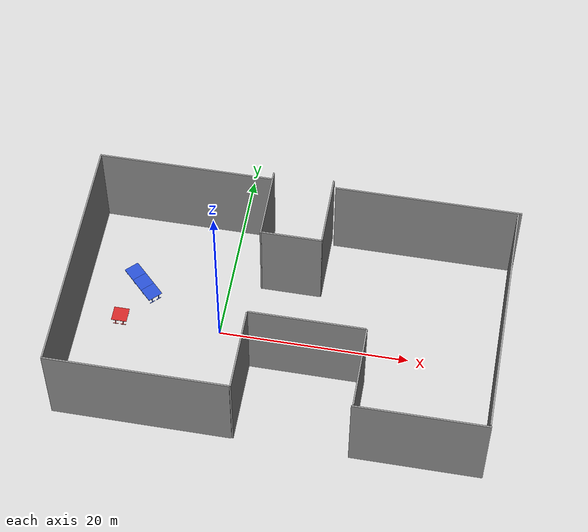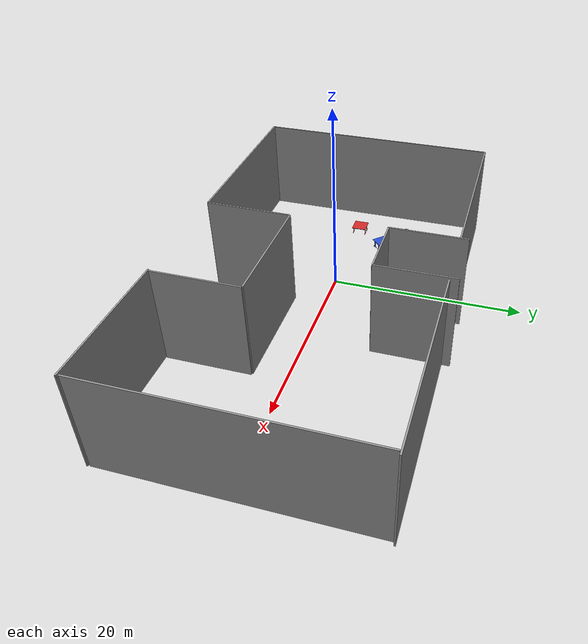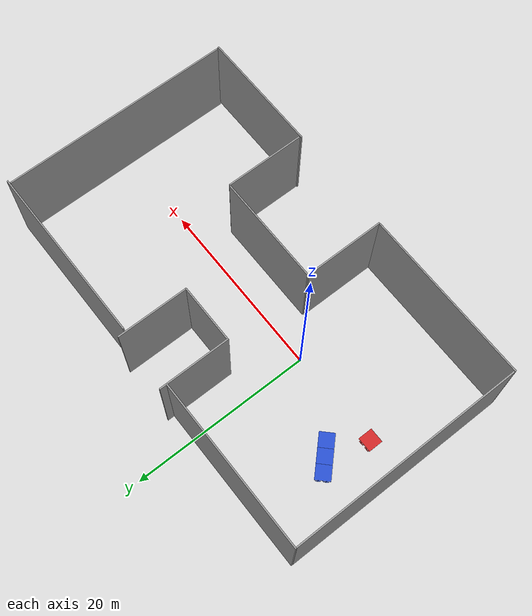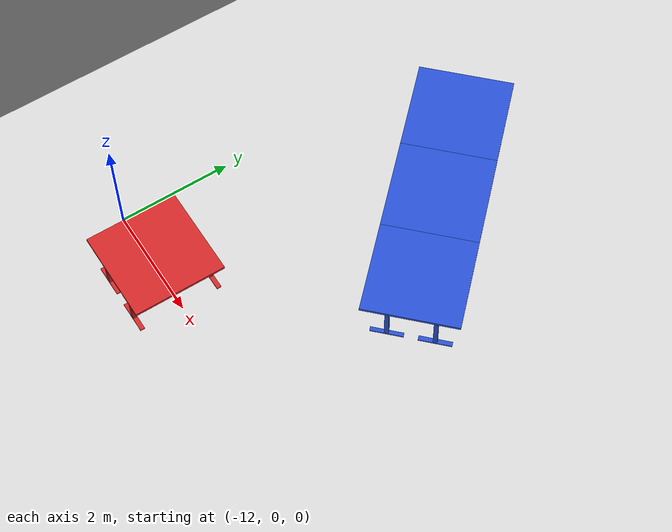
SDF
<sdf version="1.6">
 <world name="default">
  <light name="sun" type="directional">
   <pose>0 0 10 0 -0 0</pose>
   <diffuse>1 1 1 1</diffuse>
   <specular>0.2 0.2 0.2 1</specular>
   <attenuation>
    <range>1000</range>
    <constant>0.9</constant>
    <linear>0.01</linear>
    <quadratic>0.001</quadratic>
   </attenuation>
   <direction>-0.5 0.5 -1</direction>
  </light>
  <scene><ambient>1 1 1 1</ambient><background>0 0 0 0</background><shadows>0</shadows></scene>
  <gravity>0 0 -9.8</gravity>
  <magnetic_field>6e-06 2.3e-05 -4.2e-05</magnetic_field>
  <atmosphere type="adiabatic"/>
  <audio><device>default</device></audio>
  <plugin name="ros_interface_plugin" filename="librotors_gazebo_ros_interface_plugin.so"/>
  <spherical_coordinates>
   <surface_model>EARTH_WGS84</surface_model>
   <latitude_deg>47.3667</latitude_deg>
   <longitude_deg>8.55</longitude_deg>
   <elevation>500</elevation>
   <heading_deg>0</heading_deg>
  </spherical_coordinates>
  <physics name="default_physics" default="0" type="ode">
   <ode>
    <solver>
     <type>quick</type>
     <iters>1000</iters>
     <sor>1.3</sor>
     <use_dynamic_moi_rescaling>0</use_dynamic_moi_rescaling>
    </solver>
    <constraints>
     <cfm>0</cfm>
     <erp>0.2</erp>
     <contact_max_correcting_vel>100</contact_max_correcting_vel>
     <contact_surface_layer>0.001</contact_surface_layer>
    </constraints>
   </ode>
   <max_step_size>0.01</max_step_size>
   <real_time_factor>1</real_time_factor>
   <real_time_update_rate>100</real_time_update_rate>
  </physics>
  <model name="Wall_clone">
   <link name="link_0">
    <inertial>
     <mass>0.467221</mass>
     <inertia>
      <ixx>0.0398434</ixx>
      <ixy>0</ixy>
      <ixz>0</ixz>
      <iyy>0.391224</iyy>
      <iyz>0</iyz>
      <izz>0.353198</izz>
     </inertia>
    </inertial>
    <visual name="visual">
     <geometry><box><size>25.2956 0.152736 10.2725</size></box></geometry>
     <material>
      <lighting>1</lighting>
      <script><uri>file://media/materials/scripts/gazebo.material</uri><name>Gazebo/Grey</name></script>
     </material>
    </visual>
    <collision name="collision">
     <geometry><box><size>25.2956 0.152736 10.2725</size></box></geometry>
     <surface>
      <friction>
       <ode><mu>1</mu><mu2>1</mu2><fdir1>0 0 0</fdir1><slip1>0</slip1><slip2>0</slip2></ode>
       <torsional>
        <coefficient>1</coefficient>
        <patch_radius>0</patch_radius>
        <surface_radius>0</surface_radius>
        <use_patch_radius>1</use_patch_radius>
        <ode><slip>0</slip></ode>
       </torsional>
      </friction>
      <bounce><restitution_coefficient>0</restitution_coefficient><threshold>1e+06</threshold></bounce>
      <contact>
       <collide_without_contact>0</collide_without_contact>
       <collide_without_contact_bitmask>1</collide_without_contact_bitmask>
       <collide_bitmask>1</collide_bitmask>
       <ode>
        <soft_cfm>0</soft_cfm>
        <soft_erp>0.2</soft_erp>
        <kp>1e+13</kp>
        <kd>1</kd>
        <max_vel>0.01</max_vel>
        <min_depth>0</min_depth>
       </ode>
       <bullet>
        <split_impulse>1</split_impulse>
        <split_impulse_penetration_threshold>-0.01</split_impulse_penetration_threshold>
        <soft_cfm>0</soft_cfm>
        <soft_erp>0.2</soft_erp>
        <kp>1e+13</kp>
        <kd>1</kd>
       </bullet>
      </contact>
     </surface>
    </collision>
   </link>
   <static>1</static>
   <pose>29.0942 0.582122 5.05164 0 0 -1.5708</pose>
  </model>
  <model name="Wall_clone_clone">
   <link name="link_0">
    <inertial>
     <mass>0.467221</mass>
     <inertia>
      <ixx>0.0398434</ixx>
      <ixy>0</ixy>
      <ixz>0</ixz>
      <iyy>0.391224</iyy>
      <iyz>0</iyz>
      <izz>0.353198</izz>
     </inertia>
    </inertial>
    <visual name="visual">
     <geometry><box><size>25.2956 0.152736 10.2725</size></box></geometry>
     <material>
      <lighting>1</lighting>
      <script><uri>file://media/materials/scripts/gazebo.material</uri><name>Gazebo/Grey</name></script>
     </material>
    </visual>
    <collision name="collision">
     <geometry><box><size>25.2956 0.152736 10.2725</size></box></geometry>
     <surface>
      <friction>
       <ode><mu>1</mu><mu2>1</mu2><fdir1>0 0 0</fdir1><slip1>0</slip1><slip2>0</slip2></ode>
       <torsional>
        <coefficient>1</coefficient>
        <patch_radius>0</patch_radius>
        <surface_radius>0</surface_radius>
        <use_patch_radius>1</use_patch_radius>
        <ode><slip>0</slip></ode>
       </torsional>
      </friction>
      <bounce><restitution_coefficient>0</restitution_coefficient><threshold>1e+06</threshold></bounce>
      <contact>
       <collide_without_contact>0</collide_without_contact>
       <collide_without_contact_bitmask>1</collide_without_contact_bitmask>
       <collide_bitmask>1</collide_bitmask>
       <ode>
        <soft_cfm>0</soft_cfm>
        <soft_erp>0.2</soft_erp>
        <kp>1e+13</kp>
        <kd>1</kd>
        <max_vel>0.01</max_vel>
        <min_depth>0</min_depth>
       </ode>
       <bullet>
        <split_impulse>1</split_impulse>
        <split_impulse_penetration_threshold>-0.01</split_impulse_penetration_threshold>
        <soft_cfm>0</soft_cfm>
        <soft_erp>0.2</soft_erp>
        <kp>1e+13</kp>
        <kd>1</kd>
       </bullet>
      </contact>
     </surface>
    </collision>
   </link>
   <static>1</static>
   <pose>-15.1083 0.607308 5.05164 0 0 -1.5708</pose>
  </model>
  <model name="Wall_clone_clone_0">
   <link name="link_0">
    <inertial>
     <mass>0.467221</mass>
     <inertia>
      <ixx>0.0398434</ixx>
      <ixy>0</ixy>
      <ixz>0</ixz>
      <iyy>0.391224</iyy>
      <iyz>0</iyz>
      <izz>0.353198</izz>
     </inertia>
    </inertial>
    <visual name="visual">
     <geometry><box><size>18.4483 0.152736 10.2725</size></box></geometry>
     <material>
      <lighting>1</lighting>
      <script><uri>file://media/materials/scripts/gazebo.material</uri><name>Gazebo/Grey</name></script>
     </material>
    </visual>
    <collision name="collision">
     <geometry><box><size>18.4483 0.152736 10.2725</size></box></geometry>
     <surface>
      <friction>
       <ode><mu>1</mu><mu2>1</mu2><fdir1>0 0 0</fdir1><slip1>0</slip1><slip2>0</slip2></ode>
       <torsional>
        <coefficient>1</coefficient>
        <patch_radius>0</patch_radius>
        <surface_radius>0</surface_radius>
        <use_patch_radius>1</use_patch_radius>
        <ode><slip>0</slip></ode>
       </torsional>
      </friction>
      <bounce><restitution_coefficient>0</restitution_coefficient><threshold>1e+06</threshold></bounce>
      <contact>
       <collide_without_contact>0</collide_without_contact>
       <collide_without_contact_bitmask>1</collide_without_contact_bitmask>
       <collide_bitmask>1</collide_bitmask>
       <ode>
        <soft_cfm>0</soft_cfm>
        <soft_erp>0.2</soft_erp>
        <kp>1e+13</kp>
        <kd>1</kd>
        <max_vel>0.01</max_vel>
        <min_depth>0</min_depth>
       </ode>
       <bullet>
        <split_impulse>1</split_impulse>
        <split_impulse_penetration_threshold>-0.01</split_impulse_penetration_threshold>
        <soft_cfm>0</soft_cfm>
        <soft_erp>0.2</soft_erp>
        <kp>1e+13</kp>
        <kd>1</kd>
       </bullet>
      </contact>
     </surface>
    </collision>
   </link>
   <static>1</static>
   <pose>-5.94286 13.3498 5.05164 0 0 -4e-06</pose>
  </model>
  <model name="Wall_clone_clone_0_clone">
   <link name="link_0">
    <inertial>
     <mass>0.467221</mass>
     <inertia>
      <ixx>0.0398434</ixx>
      <ixy>0</ixy>
      <ixz>0</ixz>
      <iyy>0.391224</iyy>
      <iyz>0</iyz>
      <izz>0.353198</izz>
     </inertia>
    </inertial>
    <visual name="visual">
     <geometry><box><size>18.7996 0.152736 10.2725</size></box></geometry>
     <material>
      <lighting>1</lighting>
      <script><uri>file://media/materials/scripts/gazebo.material</uri><name>Gazebo/Grey</name></script>
     </material>
    </visual>
    <collision name="collision">
     <geometry><box><size>18.7996 0.152736 10.2725</size></box></geometry>
     <surface>
      <friction>
       <ode><mu>1</mu><mu2>1</mu2><fdir1>0 0 0</fdir1><slip1>0</slip1><slip2>0</slip2></ode>
       <torsional>
        <coefficient>1</coefficient>
        <patch_radius>0</patch_radius>
        <surface_radius>0</surface_radius>
        <use_patch_radius>1</use_patch_radius>
        <ode><slip>0</slip></ode>
       </torsional>
      </friction>
      <bounce><restitution_coefficient>0</restitution_coefficient><threshold>1e+06</threshold></bounce>
      <contact>
       <collide_without_contact>0</collide_without_contact>
       <collide_without_contact_bitmask>1</collide_without_contact_bitmask>
       <collide_bitmask>1</collide_bitmask>
       <ode>
        <soft_cfm>0</soft_cfm>
        <soft_erp>0.2</soft_erp>
        <kp>1e+13</kp>
        <kd>1</kd>
        <max_vel>0.01</max_vel>
        <min_depth>0</min_depth>
       </ode>
       <bullet>
        <split_impulse>1</split_impulse>
        <split_impulse_penetration_threshold>-0.01</split_impulse_penetration_threshold>
        <soft_cfm>0</soft_cfm>
        <soft_erp>0.2</soft_erp>
        <kp>1e+13</kp>
        <kd>1</kd>
       </bullet>
      </contact>
     </surface>
    </collision>
   </link>
   <static>1</static>
   <pose>-5.7854 -12.1547 5.05164 0 0 -4e-06</pose>
  </model>
  <model name="Wall_clone_clone_0_clone_clone">
   <link name="link_0">
    <inertial>
     <mass>0.467221</mass>
     <inertia>
      <ixx>0.0398434</ixx>
      <ixy>0</ixy>
      <ixz>0</ixz>
      <iyy>0.391224</iyy>
      <iyz>0</iyz>
      <izz>0.353198</izz>
     </inertia>
    </inertial>
    <visual name="visual">
     <geometry><box><size>8.74287 0.152736 10.2725</size></box></geometry>
     <material>
      <lighting>1</lighting>
      <script><uri>file://media/materials/scripts/gazebo.material</uri><name>Gazebo/Grey</name></script>
     </material>
    </visual>
    <collision name="collision">
     <geometry><box><size>8.74287 0.152736 10.2725</size></box></geometry>
     <surface>
      <friction>
       <ode><mu>1</mu><mu2>1</mu2><fdir1>0 0 0</fdir1><slip1>0</slip1><slip2>0</slip2></ode>
       <torsional>
        <coefficient>1</coefficient>
        <patch_radius>0</patch_radius>
        <surface_radius>0</surface_radius>
        <use_patch_radius>1</use_patch_radius>
        <ode><slip>0</slip></ode>
       </torsional>
      </friction>
      <bounce><restitution_coefficient>0</restitution_coefficient><threshold>1e+06</threshold></bounce>
      <contact>
       <collide_without_contact>0</collide_without_contact>
       <collide_without_contact_bitmask>1</collide_without_contact_bitmask>
       <collide_bitmask>1</collide_bitmask>
       <ode>
        <soft_cfm>0</soft_cfm>
        <soft_erp>0.2</soft_erp>
        <kp>1e+13</kp>
        <kd>1</kd>
        <max_vel>0.01</max_vel>
        <min_depth>0</min_depth>
       </ode>
       <bullet>
        <split_impulse>1</split_impulse>
        <split_impulse_penetration_threshold>-0.01</split_impulse_penetration_threshold>
        <soft_cfm>0</soft_cfm>
        <soft_erp>0.2</soft_erp>
        <kp>1e+13</kp>
        <kd>1</kd>
       </bullet>
      </contact>
     </surface>
    </collision>
   </link>
   <static>1</static>
   <pose>3.70345 -7.81343 5.05164 0 0 -1.5708</pose>
  </model>
  <model name="Wall_clone_clone_0_clone_clone_clone">
   <link name="link_0">
    <inertial>
     <mass>0.467221</mass>
     <inertia>
      <ixx>0.0398434</ixx>
      <ixy>0</ixy>
      <ixz>0</ixz>
      <iyy>0.391224</iyy>
      <iyz>0</iyz>
      <izz>0.353198</izz>
     </inertia>
    </inertial>
    <visual name="visual">
     <geometry><box><size>8.74287 0.152736 10.2725</size></box></geometry>
     <material>
      <lighting>1</lighting>
      <script><uri>file://media/materials/scripts/gazebo.material</uri><name>Gazebo/Grey</name></script>
     </material>
    </visual>
    <collision name="collision">
     <geometry><box><size>8.74287 0.152736 10.2725</size></box></geometry>
     <surface>
      <friction>
       <ode><mu>1</mu><mu2>1</mu2><fdir1>0 0 0</fdir1><slip1>0</slip1><slip2>0</slip2></ode>
       <torsional>
        <coefficient>1</coefficient>
        <patch_radius>0</patch_radius>
        <surface_radius>0</surface_radius>
        <use_patch_radius>1</use_patch_radius>
        <ode><slip>0</slip></ode>
       </torsional>
      </friction>
      <bounce><restitution_coefficient>0</restitution_coefficient><threshold>1e+06</threshold></bounce>
      <contact>
       <collide_without_contact>0</collide_without_contact>
       <collide_without_contact_bitmask>1</collide_without_contact_bitmask>
       <collide_bitmask>1</collide_bitmask>
       <ode>
        <soft_cfm>0</soft_cfm>
        <soft_erp>0.2</soft_erp>
        <kp>1e+13</kp>
        <kd>1</kd>
        <max_vel>0.01</max_vel>
        <min_depth>0</min_depth>
       </ode>
       <bullet>
        <split_impulse>1</split_impulse>
        <split_impulse_penetration_threshold>-0.01</split_impulse_penetration_threshold>
        <soft_cfm>0</soft_cfm>
        <soft_erp>0.2</soft_erp>
        <kp>1e+13</kp>
        <kd>1</kd>
       </bullet>
      </contact>
     </surface>
    </collision>
   </link>
   <static>1</static>
   <pose>15.7837 -7.77575 5.05164 0 0 -1.5708</pose>
  </model>
  <model name="Wall_clone_clone_0_clone_clone_clone_0">
   <link name="link_0">
    <inertial>
     <mass>0.467221</mass>
     <inertia>
      <ixx>0.0398434</ixx>
      <ixy>0</ixy>
      <ixz>0</ixz>
      <iyy>0.391224</iyy>
      <iyz>0</iyz>
      <izz>0.353198</izz>
     </inertia>
    </inertial>
    <visual name="visual">
     <geometry><box><size>11.9407 0.152736 10.2725</size></box></geometry>
     <material>
      <lighting>1</lighting>
      <script><uri>file://media/materials/scripts/gazebo.material</uri><name>Gazebo/Grey</name></script>
     </material>
    </visual>
    <collision name="collision">
     <geometry><box><size>11.9407 0.152736 10.2725</size></box></geometry>
     <surface>
      <friction>
       <ode><mu>1</mu><mu2>1</mu2><fdir1>0 0 0</fdir1><slip1>0</slip1><slip2>0</slip2></ode>
       <torsional>
        <coefficient>1</coefficient>
        <patch_radius>0</patch_radius>
        <surface_radius>0</surface_radius>
        <use_patch_radius>1</use_patch_radius>
        <ode><slip>0</slip></ode>
       </torsional>
      </friction>
      <bounce><restitution_coefficient>0</restitution_coefficient><threshold>1e+06</threshold></bounce>
      <contact>
       <collide_without_contact>0</collide_without_contact>
       <collide_without_contact_bitmask>1</collide_without_contact_bitmask>
       <collide_bitmask>1</collide_bitmask>
       <ode>
        <soft_cfm>0</soft_cfm>
        <soft_erp>0.2</soft_erp>
        <kp>1e+13</kp>
        <kd>1</kd>
        <max_vel>0.01</max_vel>
        <min_depth>0</min_depth>
       </ode>
       <bullet>
        <split_impulse>1</split_impulse>
        <split_impulse_penetration_threshold>-0.01</split_impulse_penetration_threshold>
        <soft_cfm>0</soft_cfm>
        <soft_erp>0.2</soft_erp>
        <kp>1e+13</kp>
        <kd>1</kd>
       </bullet>
      </contact>
     </surface>
    </collision>
   </link>
   <static>1</static>
   <pose>9.72292 -3.37629 5.05164 0 -0 3.14159</pose>
  </model>
  <model name="Wall_clone_clone_0_clone_clone_clone_0_clone">
   <link name="link_0">
    <inertial>
     <mass>0.467221</mass>
     <inertia>
      <ixx>0.0398434</ixx>
      <ixy>0</ixy>
      <ixz>0</ixz>
      <iyy>0.391224</iyy>
      <iyz>0</iyz>
      <izz>0.353198</izz>
     </inertia>
    </inertial>
    <visual name="visual">
     <geometry><box><size>13.6235 0.152736 10.2725</size></box></geometry>
     <material>
      <lighting>1</lighting>
      <script><uri>file://media/materials/scripts/gazebo.material</uri><name>Gazebo/Grey</name></script>
     </material>
    </visual>
    <collision name="collision">
     <geometry><box><size>13.6235 0.152736 10.2725</size></box></geometry>
     <surface>
      <friction>
       <ode><mu>1</mu><mu2>1</mu2><fdir1>0 0 0</fdir1><slip1>0</slip1><slip2>0</slip2></ode>
       <torsional>
        <coefficient>1</coefficient>
        <patch_radius>0</patch_radius>
        <surface_radius>0</surface_radius>
        <use_patch_radius>1</use_patch_radius>
        <ode><slip>0</slip></ode>
       </torsional>
      </friction>
      <bounce><restitution_coefficient>0</restitution_coefficient><threshold>1e+06</threshold></bounce>
      <contact>
       <collide_without_contact>0</collide_without_contact>
       <collide_without_contact_bitmask>1</collide_without_contact_bitmask>
       <collide_bitmask>1</collide_bitmask>
       <ode>
        <soft_cfm>0</soft_cfm>
        <soft_erp>0.2</soft_erp>
        <kp>1e+13</kp>
        <kd>1</kd>
        <max_vel>0.01</max_vel>
        <min_depth>0</min_depth>
       </ode>
       <bullet>
        <split_impulse>1</split_impulse>
        <split_impulse_penetration_threshold>-0.01</split_impulse_penetration_threshold>
        <soft_cfm>0</soft_cfm>
        <soft_erp>0.2</soft_erp>
        <kp>1e+13</kp>
        <kd>1</kd>
       </bullet>
      </contact>
     </surface>
    </collision>
   </link>
   <static>1</static>
   <pose>22.4064 -12.2837 5.05164 0 -0 3.14159</pose>
  </model>
  <model name="Wall_clone_clone_0_clone_clone_clone_0_clone_clone">
   <link name="link_0">
    <inertial>
     <mass>0.467221</mass>
     <inertia>
      <ixx>0.0398434</ixx>
      <ixy>0</ixy>
      <ixz>0</ixz>
      <iyy>0.391224</iyy>
      <iyz>0</iyz>
      <izz>0.353198</izz>
     </inertia>
    </inertial>
    <visual name="visual">
     <geometry><box><size>19.4955 0.152736 10.2725</size></box></geometry>
     <material>
      <lighting>1</lighting>
      <script><uri>file://media/materials/scripts/gazebo.material</uri><name>Gazebo/Grey</name></script>
     </material>
    </visual>
    <collision name="collision">
     <geometry><box><size>19.4955 0.152736 10.2725</size></box></geometry>
     <surface>
      <friction>
       <ode><mu>1</mu><mu2>1</mu2><fdir1>0 0 0</fdir1><slip1>0</slip1><slip2>0</slip2></ode>
       <torsional>
        <coefficient>1</coefficient>
        <patch_radius>0</patch_radius>
        <surface_radius>0</surface_radius>
        <use_patch_radius>1</use_patch_radius>
        <ode><slip>0</slip></ode>
       </torsional>
      </friction>
      <bounce><restitution_coefficient>0</restitution_coefficient><threshold>1e+06</threshold></bounce>
      <contact>
       <collide_without_contact>0</collide_without_contact>
       <collide_without_contact_bitmask>1</collide_without_contact_bitmask>
       <collide_bitmask>1</collide_bitmask>
       <ode>
        <soft_cfm>0</soft_cfm>
        <soft_erp>0.2</soft_erp>
        <kp>1e+13</kp>
        <kd>1</kd>
        <max_vel>0.01</max_vel>
        <min_depth>0</min_depth>
       </ode>
       <bullet>
        <split_impulse>1</split_impulse>
        <split_impulse_penetration_threshold>-0.01</split_impulse_penetration_threshold>
        <soft_cfm>0</soft_cfm>
        <soft_erp>0.2</soft_erp>
        <kp>1e+13</kp>
        <kd>1</kd>
       </bullet>
      </contact>
     </surface>
    </collision>
   </link>
   <static>1</static>
   <pose>19.728 13.3426 5.05164 0 -0 3.14159</pose>
  </model>
  <model name="Wall_clone_clone_0_clone_clone_clone_1">
   <link name="link_0">
    <inertial>
     <mass>0.467221</mass>
     <inertia>
      <ixx>0.0398434</ixx>
      <ixy>0</ixy>
      <ixz>0</ixz>
      <iyy>0.391224</iyy>
      <iyz>0</iyz>
      <izz>0.353198</izz>
     </inertia>
    </inertial>
    <visual name="visual">
     <geometry><box><size>7.81661 0.152736 10.2725</size></box></geometry>
     <material>
      <lighting>1</lighting>
      <script><uri>file://media/materials/scripts/gazebo.material</uri><name>Gazebo/Grey</name></script>
     </material>
    </visual>
    <collision name="collision">
     <geometry><box><size>7.81661 0.152736 10.2725</size></box></geometry>
     <surface>
      <friction>
       <ode><mu>1</mu><mu2>1</mu2><fdir1>0 0 0</fdir1><slip1>0</slip1><slip2>0</slip2></ode>
       <torsional>
        <coefficient>1</coefficient>
        <patch_radius>0</patch_radius>
        <surface_radius>0</surface_radius>
        <use_patch_radius>1</use_patch_radius>
        <ode><slip>0</slip></ode>
       </torsional>
      </friction>
      <bounce><restitution_coefficient>0</restitution_coefficient><threshold>1e+06</threshold></bounce>
      <contact>
       <collide_without_contact>0</collide_without_contact>
       <collide_without_contact_bitmask>1</collide_without_contact_bitmask>
       <collide_bitmask>1</collide_bitmask>
       <ode>
        <soft_cfm>0</soft_cfm>
        <soft_erp>0.2</soft_erp>
        <kp>1e+13</kp>
        <kd>1</kd>
        <max_vel>0.01</max_vel>
        <min_depth>0</min_depth>
       </ode>
       <bullet>
        <split_impulse>1</split_impulse>
        <split_impulse_penetration_threshold>-0.01</split_impulse_penetration_threshold>
        <soft_cfm>0</soft_cfm>
        <soft_erp>0.2</soft_erp>
        <kp>1e+13</kp>
        <kd>1</kd>
       </bullet>
      </contact>
     </surface>
    </collision>
   </link>
   <static>1</static>
   <pose>3.2879 10.2519 5.05164 0 0 -1.5708</pose>
  </model>
  <model name="Wall_clone_clone_0_clone_clone_clone_1_clone">
   <link name="link_0">
    <inertial>
     <mass>0.467221</mass>
     <inertia>
      <ixx>0.0398434</ixx>
      <ixy>0</ixy>
      <ixz>0</ixz>
      <iyy>0.391224</iyy>
      <iyz>0</iyz>
      <izz>0.353198</izz>
     </inertia>
    </inertial>
    <visual name="visual">
     <geometry><box><size>6.31047 0.152736 10.2725</size></box></geometry>
     <material>
      <lighting>1</lighting>
      <script><uri>file://media/materials/scripts/gazebo.material</uri><name>Gazebo/Grey</name></script>
     </material>
    </visual>
    <collision name="collision">
     <geometry><box><size>6.31047 0.152736 10.2725</size></box></geometry>
     <surface>
      <friction>
       <ode><mu>1</mu><mu2>1</mu2><fdir1>0 0 0</fdir1><slip1>0</slip1><slip2>0</slip2></ode>
       <torsional>
        <coefficient>1</coefficient>
        <patch_radius>0</patch_radius>
        <surface_radius>0</surface_radius>
        <use_patch_radius>1</use_patch_radius>
        <ode><slip>0</slip></ode>
       </torsional>
      </friction>
      <bounce><restitution_coefficient>0</restitution_coefficient><threshold>1e+06</threshold></bounce>
      <contact>
       <collide_without_contact>0</collide_without_contact>
       <collide_without_contact_bitmask>1</collide_without_contact_bitmask>
       <collide_bitmask>1</collide_bitmask>
       <ode>
        <soft_cfm>0</soft_cfm>
        <soft_erp>0.2</soft_erp>
        <kp>1e+13</kp>
        <kd>1</kd>
        <max_vel>0.01</max_vel>
        <min_depth>0</min_depth>
       </ode>
       <bullet>
        <split_impulse>1</split_impulse>
        <split_impulse_penetration_threshold>-0.01</split_impulse_penetration_threshold>
        <soft_cfm>0</soft_cfm>
        <soft_erp>0.2</soft_erp>
        <kp>1e+13</kp>
        <kd>1</kd>
       </bullet>
      </contact>
     </surface>
    </collision>
   </link>
   <static>1</static>
   <pose>6.51204 6.43694 5.05164 0 -0 3.14159</pose>
  </model>
  <model name="Wall_clone_clone_0_clone_clone_clone_1_clone_0">
   <link name="link_0">
    <inertial>
     <mass>0.467221</mass>
     <inertia>
      <ixx>0.0398434</ixx>
      <ixy>0</ixy>
      <ixz>0</ixz>
      <iyy>0.391224</iyy>
      <iyz>0</iyz>
      <izz>0.353198</izz>
     </inertia>
    </inertial>
    <visual name="visual">
     <geometry><box><size>7.81662 0.152736 10.2725</size></box></geometry>
     <material>
      <lighting>1</lighting>
      <script><uri>file://media/materials/scripts/gazebo.material</uri><name>Gazebo/Grey</name></script>
     </material>
    </visual>
    <collision name="collision">
     <geometry><box><size>7.81662 0.152736 10.2725</size></box></geometry>
     <surface>
      <friction>
       <ode><mu>1</mu><mu2>1</mu2><fdir1>0 0 0</fdir1><slip1>0</slip1><slip2>0</slip2></ode>
       <torsional>
        <coefficient>1</coefficient>
        <patch_radius>0</patch_radius>
        <surface_radius>0</surface_radius>
        <use_patch_radius>1</use_patch_radius>
        <ode><slip>0</slip></ode>
       </torsional>
      </friction>
      <bounce><restitution_coefficient>0</restitution_coefficient><threshold>1e+06</threshold></bounce>
      <contact>
       <collide_without_contact>0</collide_without_contact>
       <collide_without_contact_bitmask>1</collide_without_contact_bitmask>
       <collide_bitmask>1</collide_bitmask>
       <ode>
        <soft_cfm>0</soft_cfm>
        <soft_erp>0.2</soft_erp>
        <kp>1e+13</kp>
        <kd>1</kd>
        <max_vel>0.01</max_vel>
        <min_depth>0</min_depth>
       </ode>
       <bullet>
        <split_impulse>1</split_impulse>
        <split_impulse_penetration_threshold>-0.01</split_impulse_penetration_threshold>
        <soft_cfm>0</soft_cfm>
        <soft_erp>0.2</soft_erp>
        <kp>1e+13</kp>
        <kd>1</kd>
       </bullet>
      </contact>
     </surface>
    </collision>
   </link>
   <static>1</static>
   <pose>9.64965 10.2933 5.05164 0 0 -1.5708</pose>
  </model>
  <model name="table_train_blue">
   <link name="link_1">
    <inertial>
     <mass>0.00101438</mass>
     <inertia>
      <ixx>5.68699e-07</ixx>
      <ixy>0</ixy>
      <ixz>0</ixz>
      <iyy>2.6602e-05</iyy>
      <iyz>0</iyz>
      <izz>2.70816e-05</izz>
     </inertia>
    </inertial>
    <pose>0.401616 0.715267 -0.253214 0 -0 0</pose>
    <visual name="visual">
     <geometry><box><size>0.560509 0.078742 0.022963</size></box></geometry>
     <material>
      <lighting>1</lighting>
      <script><uri>file://media/materials/scripts/gazebo.material</uri><name>Gazebo/Blue</name></script>
     </material>
    </visual>
    <collision name="collision">
     <geometry><box><size>0.560509 0.078742 0.022963</size></box></geometry>
     <surface>
      <friction>
       <ode><mu>1</mu><mu2>1</mu2><fdir1>0 0 0</fdir1><slip1>0</slip1><slip2>0</slip2></ode>
       <torsional>
        <coefficient>1</coefficient>
        <patch_radius>0</patch_radius>
        <surface_radius>0</surface_radius>
        <use_patch_radius>1</use_patch_radius>
        <ode><slip>0</slip></ode>
       </torsional>
      </friction>
      <bounce><restitution_coefficient>0</restitution_coefficient><threshold>1e+06</threshold></bounce>
      <contact>
       <collide_without_contact>0</collide_without_contact>
       <collide_without_contact_bitmask>1</collide_without_contact_bitmask>
       <collide_bitmask>1</collide_bitmask>
       <ode>
        <soft_cfm>0</soft_cfm>
        <soft_erp>0.2</soft_erp>
        <kp>1e+13</kp>
        <kd>1</kd>
        <max_vel>0.01</max_vel>
        <min_depth>0</min_depth>
       </ode>
       <bullet>
        <split_impulse>1</split_impulse>
        <split_impulse_penetration_threshold>-0.01</split_impulse_penetration_threshold>
        <soft_cfm>0</soft_cfm>
        <soft_erp>0.2</soft_erp>
        <kp>1e+13</kp>
        <kd>1</kd>
       </bullet>
      </contact>
     </surface>
    </collision>
   </link>
   <link name="link_1_clone">
    <inertial>
     <mass>0.00091121</mass>
     <inertia>
      <ixx>4.19417e-07</ixx>
      <ixy>0</ixy>
      <ixz>0</ixz>
      <iyy>2.38963e-05</iyy>
      <iyz>0</iyz>
      <izz>2.42357e-05</izz>
     </inertia>
    </inertial>
    <pose>-0.397753 0.712784 -0.253214 0 -0 0</pose>
    <visual name="visual">
     <geometry><box><size>0.560509 0.070683 0.022963</size></box></geometry>
     <material>
      <lighting>1</lighting>
      <script><uri>file://media/materials/scripts/gazebo.material</uri><name>Gazebo/Blue</name></script>
      <shader type="pixel"/>
     </material>
    </visual>
    <collision name="collision">
     <geometry><box><size>0.560509 0.070683 0.022963</size></box></geometry>
     <surface>
      <friction>
       <ode><mu>1</mu><mu2>1</mu2><fdir1>0 0 0</fdir1><slip1>0</slip1><slip2>0</slip2></ode>
       <torsional>
        <coefficient>1</coefficient>
        <patch_radius>0</patch_radius>
        <surface_radius>0</surface_radius>
        <use_patch_radius>1</use_patch_radius>
        <ode><slip>0</slip></ode>
       </torsional>
      </friction>
      <bounce><restitution_coefficient>0</restitution_coefficient><threshold>1e+06</threshold></bounce>
      <contact>
       <collide_without_contact>0</collide_without_contact>
       <collide_without_contact_bitmask>1</collide_without_contact_bitmask>
       <collide_bitmask>1</collide_bitmask>
       <ode>
        <soft_cfm>0</soft_cfm>
        <soft_erp>0.2</soft_erp>
        <kp>1e+13</kp>
        <kd>1</kd>
        <max_vel>0.01</max_vel>
        <min_depth>0</min_depth>
       </ode>
       <bullet>
        <split_impulse>1</split_impulse>
        <split_impulse_penetration_threshold>-0.01</split_impulse_penetration_threshold>
        <soft_cfm>0</soft_cfm>
        <soft_erp>0.2</soft_erp>
        <kp>1e+13</kp>
        <kd>1</kd>
       </bullet>
      </contact>
     </surface>
    </collision>
   </link>
   <link name="link_1_clone_0">
    <inertial>
     <mass>0.00101881</mass>
     <inertia>
      <ixx>5.74997e-07</ixx>
      <ixy>0</ixy>
      <ixz>0</ixz>
      <iyy>2.67181e-05</iyy>
      <iyz>0</iyz>
      <izz>2.72035e-05</izz>
     </inertia>
    </inertial>
    <pose>0.402245 -0.712752 -0.253214 0 -0 0</pose>
    <visual name="visual">
     <geometry><box><size>0.560509 0.079027 0.022963</size></box></geometry>
     <material>
      <lighting>1</lighting>
      <script><uri>file://media/materials/scripts/gazebo.material</uri><name>Gazebo/Blue</name></script>
      <shader type="pixel"/>
     </material>
    </visual>
    <collision name="collision">
     <geometry><box><size>0.560509 0.079027 0.022963</size></box></geometry>
     <surface>
      <friction>
       <ode><mu>1</mu><mu2>1</mu2><fdir1>0 0 0</fdir1><slip1>0</slip1><slip2>0</slip2></ode>
       <torsional>
        <coefficient>1</coefficient>
        <patch_radius>0</patch_radius>
        <surface_radius>0</surface_radius>
        <use_patch_radius>1</use_patch_radius>
        <ode><slip>0</slip></ode>
       </torsional>
      </friction>
      <bounce><restitution_coefficient>0</restitution_coefficient><threshold>1e+06</threshold></bounce>
      <contact>
       <collide_without_contact>0</collide_without_contact>
       <collide_without_contact_bitmask>1</collide_without_contact_bitmask>
       <collide_bitmask>1</collide_bitmask>
       <ode>
        <soft_cfm>0</soft_cfm>
        <soft_erp>0.2</soft_erp>
        <kp>1e+13</kp>
        <kd>1</kd>
        <max_vel>0.01</max_vel>
        <min_depth>0</min_depth>
       </ode>
       <bullet>
        <split_impulse>1</split_impulse>
        <split_impulse_penetration_threshold>-0.01</split_impulse_penetration_threshold>
        <soft_cfm>0</soft_cfm>
        <soft_erp>0.2</soft_erp>
        <kp>1e+13</kp>
        <kd>1</kd>
       </bullet>
      </contact>
     </surface>
    </collision>
   </link>
   <link name="link_1_clone_1">
    <inertial>
     <mass>0.00091121</mass>
     <inertia>
      <ixx>4.19417e-07</ixx>
      <ixy>0</ixy>
      <ixz>0</ixz>
      <iyy>2.38963e-05</iyy>
      <iyz>0</iyz>
      <izz>2.42357e-05</izz>
     </inertia>
    </inertial>
    <pose>-0.395448 -0.713621 -0.253214 0 -0 0</pose>
    <visual name="visual">
     <geometry><box><size>0.560509 0.070683 0.022963</size></box></geometry>
     <material>
      <lighting>1</lighting>
      <script><uri>file://media/materials/scripts/gazebo.material</uri><name>Gazebo/Blue</name></script>
      <shader type="pixel"/>
     </material>
    </visual>
    <collision name="collision">
     <geometry><box><size>0.560509 0.070683 0.022963</size></box></geometry>
     <surface>
      <friction>
       <ode><mu>1</mu><mu2>1</mu2><fdir1>0 0 0</fdir1><slip1>0</slip1><slip2>0</slip2></ode>
       <torsional>
        <coefficient>1</coefficient>
        <patch_radius>0</patch_radius>
        <surface_radius>0</surface_radius>
        <use_patch_radius>1</use_patch_radius>
        <ode><slip>0</slip></ode>
       </torsional>
      </friction>
      <bounce><restitution_coefficient>0</restitution_coefficient><threshold>1e+06</threshold></bounce>
      <contact>
       <collide_without_contact>0</collide_without_contact>
       <collide_without_contact_bitmask>1</collide_without_contact_bitmask>
       <collide_bitmask>1</collide_bitmask>
       <ode>
        <soft_cfm>0</soft_cfm>
        <soft_erp>0.2</soft_erp>
        <kp>1e+13</kp>
        <kd>1</kd>
        <max_vel>0.01</max_vel>
        <min_depth>0</min_depth>
       </ode>
       <bullet>
        <split_impulse>1</split_impulse>
        <split_impulse_penetration_threshold>-0.01</split_impulse_penetration_threshold>
        <soft_cfm>0</soft_cfm>
        <soft_erp>0.2</soft_erp>
        <kp>1e+13</kp>
        <kd>1</kd>
       </bullet>
      </contact>
     </surface>
    </collision>
   </link>
   <link name="link_1_clone_2">
    <inertial>
     <mass>0.00374954</mass>
     <inertia>
      <ixx>0.000173692</ixx>
      <ixy>0</ixy>
      <ixz>0</ixz>
      <iyy>0.000173716</iyy>
      <iyz>0</iyz>
      <izz>3.14587e-06</izz>
     </inertia>
    </inertial>
    <pose>0.400365 0.715374 0.127721 0 -0 0</pose>
    <visual name="visual">
     <geometry><box><size>0.071217 0.070683 0.742218</size></box></geometry>
     <material>
      <lighting>1</lighting>
      <script><uri>file://media/materials/scripts/gazebo.material</uri><name>Gazebo/Blue</name></script>
      <shader type="pixel"/>
     </material>
    </visual>
    <collision name="collision">
     <geometry><box><size>0.071217 0.070683 0.742218</size></box></geometry>
     <surface>
      <friction>
       <ode><mu>1</mu><mu2>1</mu2><fdir1>0 0 0</fdir1><slip1>0</slip1><slip2>0</slip2></ode>
       <torsional>
        <coefficient>1</coefficient>
        <patch_radius>0</patch_radius>
        <surface_radius>0</surface_radius>
        <use_patch_radius>1</use_patch_radius>
        <ode><slip>0</slip></ode>
       </torsional>
      </friction>
      <bounce><restitution_coefficient>0</restitution_coefficient><threshold>1e+06</threshold></bounce>
      <contact>
       <collide_without_contact>0</collide_without_contact>
       <collide_without_contact_bitmask>1</collide_without_contact_bitmask>
       <collide_bitmask>1</collide_bitmask>
       <ode>
        <soft_cfm>0</soft_cfm>
        <soft_erp>0.2</soft_erp>
        <kp>1e+13</kp>
        <kd>1</kd>
        <max_vel>0.01</max_vel>
        <min_depth>0</min_depth>
       </ode>
       <bullet>
        <split_impulse>1</split_impulse>
        <split_impulse_penetration_threshold>-0.01</split_impulse_penetration_threshold>
        <soft_cfm>0</soft_cfm>
        <soft_erp>0.2</soft_erp>
        <kp>1e+13</kp>
        <kd>1</kd>
       </bullet>
      </contact>
     </surface>
    </collision>
   </link>
   <link name="link_1_clone_2_clone">
    <inertial>
     <mass>0.00374954</mass>
     <inertia>
      <ixx>0.000173692</ixx>
      <ixy>0</ixy>
      <ixz>0</ixz>
      <iyy>0.000173716</iyy>
      <iyz>0</iyz>
      <izz>3.14587e-06</izz>
     </inertia>
    </inertial>
    <pose>0.400909 -0.713133 0.127721 0 -0 0</pose>
    <visual name="visual">
     <geometry><box><size>0.071217 0.070683 0.742218</size></box></geometry>
     <material>
      <lighting>1</lighting>
      <script><uri>file://media/materials/scripts/gazebo.material</uri><name>Gazebo/Blue</name></script>
      <shader type="pixel"/>
     </material>
    </visual>
    <collision name="collision">
     <geometry><box><size>0.071217 0.070683 0.742218</size></box></geometry>
     <surface>
      <friction>
       <ode><mu>1</mu><mu2>1</mu2><fdir1>0 0 0</fdir1><slip1>0</slip1><slip2>0</slip2></ode>
       <torsional>
        <coefficient>1</coefficient>
        <patch_radius>0</patch_radius>
        <surface_radius>0</surface_radius>
        <use_patch_radius>1</use_patch_radius>
        <ode><slip>0</slip></ode>
       </torsional>
      </friction>
      <bounce><restitution_coefficient>0</restitution_coefficient><threshold>1e+06</threshold></bounce>
      <contact>
       <collide_without_contact>0</collide_without_contact>
       <collide_without_contact_bitmask>1</collide_without_contact_bitmask>
       <collide_bitmask>1</collide_bitmask>
       <ode>
        <soft_cfm>0</soft_cfm>
        <soft_erp>0.2</soft_erp>
        <kp>1e+13</kp>
        <kd>1</kd>
        <max_vel>0.01</max_vel>
        <min_depth>0</min_depth>
       </ode>
       <bullet>
        <split_impulse>1</split_impulse>
        <split_impulse_penetration_threshold>-0.01</split_impulse_penetration_threshold>
        <soft_cfm>0</soft_cfm>
        <soft_erp>0.2</soft_erp>
        <kp>1e+13</kp>
        <kd>1</kd>
       </bullet>
      </contact>
     </surface>
    </collision>
   </link>
   <link name="link_1_clone_2_clone_0">
    <inertial>
     <mass>0.00374954</mass>
     <inertia>
      <ixx>0.000173692</ixx>
      <ixy>0</ixy>
      <ixz>0</ixz>
      <iyy>0.000173716</iyy>
      <iyz>0</iyz>
      <izz>3.14587e-06</izz>
     </inertia>
    </inertial>
    <pose>-0.397388 0.712627 0.127721 0 -0 0</pose>
    <visual name="visual">
     <geometry><box><size>0.071217 0.070683 0.742218</size></box></geometry>
     <material>
      <lighting>1</lighting>
      <script><uri>file://media/materials/scripts/gazebo.material</uri><name>Gazebo/Blue</name></script>
      <shader type="pixel"/>
     </material>
    </visual>
    <collision name="collision">
     <geometry><box><size>0.071217 0.070683 0.742218</size></box></geometry>
     <surface>
      <friction>
       <ode><mu>1</mu><mu2>1</mu2><fdir1>0 0 0</fdir1><slip1>0</slip1><slip2>0</slip2></ode>
       <torsional>
        <coefficient>1</coefficient>
        <patch_radius>0</patch_radius>
        <surface_radius>0</surface_radius>
        <use_patch_radius>1</use_patch_radius>
        <ode><slip>0</slip></ode>
       </torsional>
      </friction>
      <bounce><restitution_coefficient>0</restitution_coefficient><threshold>1e+06</threshold></bounce>
      <contact>
       <collide_without_contact>0</collide_without_contact>
       <collide_without_contact_bitmask>1</collide_without_contact_bitmask>
       <collide_bitmask>1</collide_bitmask>
       <ode>
        <soft_cfm>0</soft_cfm>
        <soft_erp>0.2</soft_erp>
        <kp>1e+13</kp>
        <kd>1</kd>
        <max_vel>0.01</max_vel>
        <min_depth>0</min_depth>
       </ode>
       <bullet>
        <split_impulse>1</split_impulse>
        <split_impulse_penetration_threshold>-0.01</split_impulse_penetration_threshold>
        <soft_cfm>0</soft_cfm>
        <soft_erp>0.2</soft_erp>
        <kp>1e+13</kp>
        <kd>1</kd>
       </bullet>
      </contact>
     </surface>
    </collision>
   </link>
   <link name="link_1_clone_2_clone_1">
    <inertial>
     <mass>0.00374954</mass>
     <inertia>
      <ixx>0.000173692</ixx>
      <ixy>0</ixy>
      <ixz>0</ixz>
      <iyy>0.000173716</iyy>
      <iyz>0</iyz>
      <izz>3.14587e-06</izz>
     </inertia>
    </inertial>
    <pose>-0.397853 -0.713469 0.127721 0 -0 0</pose>
    <visual name="visual">
     <geometry><box><size>0.071217 0.070683 0.742218</size></box></geometry>
     <material>
      <lighting>1</lighting>
      <script><uri>file://media/materials/scripts/gazebo.material</uri><name>Gazebo/Blue</name></script>
      <shader type="pixel"/>
     </material>
    </visual>
    <collision name="collision">
     <geometry><box><size>0.071217 0.070683 0.742218</size></box></geometry>
     <surface>
      <friction>
       <ode><mu>1</mu><mu2>1</mu2><fdir1>0 0 0</fdir1><slip1>0</slip1><slip2>0</slip2></ode>
       <torsional>
        <coefficient>1</coefficient>
        <patch_radius>0</patch_radius>
        <surface_radius>0</surface_radius>
        <use_patch_radius>1</use_patch_radius>
        <ode><slip>0</slip></ode>
       </torsional>
      </friction>
      <bounce><restitution_coefficient>0</restitution_coefficient><threshold>1e+06</threshold></bounce>
      <contact>
       <collide_without_contact>0</collide_without_contact>
       <collide_without_contact_bitmask>1</collide_without_contact_bitmask>
       <collide_bitmask>1</collide_bitmask>
       <ode>
        <soft_cfm>0</soft_cfm>
        <soft_erp>0.2</soft_erp>
        <kp>1e+13</kp>
        <kd>1</kd>
        <max_vel>0.01</max_vel>
        <min_depth>0</min_depth>
       </ode>
       <bullet>
        <split_impulse>1</split_impulse>
        <split_impulse_penetration_threshold>-0.01</split_impulse_penetration_threshold>
        <soft_cfm>0</soft_cfm>
        <soft_erp>0.2</soft_erp>
        <kp>1e+13</kp>
        <kd>1</kd>
       </bullet>
      </contact>
     </surface>
    </collision>
   </link>
   <link name="link_3">
    <inertial>
     <mass>0.128642</mass>
     <inertia>
      <ixx>0.0279879</ixx>
      <ixy>0</ixy>
      <ixz>0</ixz>
      <iyy>0.0287996</iyy>
      <iyz>0</iyz>
      <izz>0.0567363</izz>
     </inertia>
    </inertial>
    <pose>-0.01669 -0.003076 0.501974 0 -0 0</pose>
    <visual name="visual">
     <geometry><box><size>1.63832 1.61505 0.04888</size></box></geometry>
     <material>
      <lighting>1</lighting>
      <script><uri>file://media/materials/scripts/gazebo.material</uri><name>Gazebo/Blue</name></script>
     </material>
    </visual>
    <collision name="collision">
     <geometry><box><size>1.63832 1.61505 0.04888</size></box></geometry>
     <surface>
      <friction>
       <ode><mu>1</mu><mu2>1</mu2><fdir1>0 0 0</fdir1><slip1>0</slip1><slip2>0</slip2></ode>
       <torsional>
        <coefficient>1</coefficient>
        <patch_radius>0</patch_radius>
        <surface_radius>0</surface_radius>
        <use_patch_radius>1</use_patch_radius>
        <ode><slip>0</slip></ode>
       </torsional>
      </friction>
      <bounce><restitution_coefficient>0</restitution_coefficient><threshold>1e+06</threshold></bounce>
      <contact>
       <collide_without_contact>0</collide_without_contact>
       <collide_without_contact_bitmask>1</collide_without_contact_bitmask>
       <collide_bitmask>1</collide_bitmask>
       <ode>
        <soft_cfm>0</soft_cfm>
        <soft_erp>0.2</soft_erp>
        <kp>1e+13</kp>
        <kd>1</kd>
        <max_vel>0.01</max_vel>
        <min_depth>0</min_depth>
       </ode>
       <bullet>
        <split_impulse>1</split_impulse>
        <split_impulse_penetration_threshold>-0.01</split_impulse_penetration_threshold>
        <soft_cfm>0</soft_cfm>
        <soft_erp>0.2</soft_erp>
        <kp>1e+13</kp>
        <kd>1</kd>
       </bullet>
      </contact>
     </surface>
    </collision>
   </link>
   <static>1</static>
   <pose>-8.06767 3.33945 0.267841 0 -0 0.785398</pose>
  </model>
  <model name="table_train_blue_clone">
   <link name="link_1">
    <inertial>
     <mass>0.00101438</mass>
     <inertia>
      <ixx>5.68699e-07</ixx>
      <ixy>0</ixy>
      <ixz>0</ixz>
      <iyy>2.6602e-05</iyy>
      <iyz>0</iyz>
      <izz>2.70816e-05</izz>
     </inertia>
    </inertial>
    <pose>0.401616 0.715267 -0.253214 0 -0 0</pose>
    <visual name="visual">
     <geometry><box><size>0.560509 0.078742 0.022963</size></box></geometry>
     <material>
      <lighting>1</lighting>
      <script><uri>file://media/materials/scripts/gazebo.material</uri><name>Gazebo/Blue</name></script>
     </material>
    </visual>
    <collision name="collision">
     <geometry><box><size>0.560509 0.078742 0.022963</size></box></geometry>
     <surface>
      <friction>
       <ode><mu>1</mu><mu2>1</mu2><fdir1>0 0 0</fdir1><slip1>0</slip1><slip2>0</slip2></ode>
       <torsional>
        <coefficient>1</coefficient>
        <patch_radius>0</patch_radius>
        <surface_radius>0</surface_radius>
        <use_patch_radius>1</use_patch_radius>
        <ode><slip>0</slip></ode>
       </torsional>
      </friction>
      <bounce><restitution_coefficient>0</restitution_coefficient><threshold>1e+06</threshold></bounce>
      <contact>
       <collide_without_contact>0</collide_without_contact>
       <collide_without_contact_bitmask>1</collide_without_contact_bitmask>
       <collide_bitmask>1</collide_bitmask>
       <ode>
        <soft_cfm>0</soft_cfm>
        <soft_erp>0.2</soft_erp>
        <kp>1e+13</kp>
        <kd>1</kd>
        <max_vel>0.01</max_vel>
        <min_depth>0</min_depth>
       </ode>
       <bullet>
        <split_impulse>1</split_impulse>
        <split_impulse_penetration_threshold>-0.01</split_impulse_penetration_threshold>
        <soft_cfm>0</soft_cfm>
        <soft_erp>0.2</soft_erp>
        <kp>1e+13</kp>
        <kd>1</kd>
       </bullet>
      </contact>
     </surface>
    </collision>
   </link>
   <link name="link_1_clone">
    <inertial>
     <mass>0.00091121</mass>
     <inertia>
      <ixx>4.19417e-07</ixx>
      <ixy>0</ixy>
      <ixz>0</ixz>
      <iyy>2.38963e-05</iyy>
      <iyz>0</iyz>
      <izz>2.42357e-05</izz>
     </inertia>
    </inertial>
    <pose>-0.397753 0.712784 -0.253214 0 -0 0</pose>
    <visual name="visual">
     <geometry><box><size>0.560509 0.070683 0.022963</size></box></geometry>
     <material>
      <lighting>1</lighting>
      <script><uri>file://media/materials/scripts/gazebo.material</uri><name>Gazebo/Blue</name></script>
      <shader type="pixel"/>
     </material>
    </visual>
    <collision name="collision">
     <geometry><box><size>0.560509 0.070683 0.022963</size></box></geometry>
     <surface>
      <friction>
       <ode><mu>1</mu><mu2>1</mu2><fdir1>0 0 0</fdir1><slip1>0</slip1><slip2>0</slip2></ode>
       <torsional>
        <coefficient>1</coefficient>
        <patch_radius>0</patch_radius>
        <surface_radius>0</surface_radius>
        <use_patch_radius>1</use_patch_radius>
        <ode><slip>0</slip></ode>
       </torsional>
      </friction>
      <bounce><restitution_coefficient>0</restitution_coefficient><threshold>1e+06</threshold></bounce>
      <contact>
       <collide_without_contact>0</collide_without_contact>
       <collide_without_contact_bitmask>1</collide_without_contact_bitmask>
       <collide_bitmask>1</collide_bitmask>
       <ode>
        <soft_cfm>0</soft_cfm>
        <soft_erp>0.2</soft_erp>
        <kp>1e+13</kp>
        <kd>1</kd>
        <max_vel>0.01</max_vel>
        <min_depth>0</min_depth>
       </ode>
       <bullet>
        <split_impulse>1</split_impulse>
        <split_impulse_penetration_threshold>-0.01</split_impulse_penetration_threshold>
        <soft_cfm>0</soft_cfm>
        <soft_erp>0.2</soft_erp>
        <kp>1e+13</kp>
        <kd>1</kd>
       </bullet>
      </contact>
     </surface>
    </collision>
   </link>
   <link name="link_1_clone_0">
    <inertial>
     <mass>0.00101881</mass>
     <inertia>
      <ixx>5.74997e-07</ixx>
      <ixy>0</ixy>
      <ixz>0</ixz>
      <iyy>2.67181e-05</iyy>
      <iyz>0</iyz>
      <izz>2.72035e-05</izz>
     </inertia>
    </inertial>
    <pose>0.402245 -0.712752 -0.253214 0 -0 0</pose>
    <visual name="visual">
     <geometry><box><size>0.560509 0.079027 0.022963</size></box></geometry>
     <material>
      <lighting>1</lighting>
      <script><uri>file://media/materials/scripts/gazebo.material</uri><name>Gazebo/Blue</name></script>
      <shader type="pixel"/>
     </material>
    </visual>
    <collision name="collision">
     <geometry><box><size>0.560509 0.079027 0.022963</size></box></geometry>
     <surface>
      <friction>
       <ode><mu>1</mu><mu2>1</mu2><fdir1>0 0 0</fdir1><slip1>0</slip1><slip2>0</slip2></ode>
       <torsional>
        <coefficient>1</coefficient>
        <patch_radius>0</patch_radius>
        <surface_radius>0</surface_radius>
        <use_patch_radius>1</use_patch_radius>
        <ode><slip>0</slip></ode>
       </torsional>
      </friction>
      <bounce><restitution_coefficient>0</restitution_coefficient><threshold>1e+06</threshold></bounce>
      <contact>
       <collide_without_contact>0</collide_without_contact>
       <collide_without_contact_bitmask>1</collide_without_contact_bitmask>
       <collide_bitmask>1</collide_bitmask>
       <ode>
        <soft_cfm>0</soft_cfm>
        <soft_erp>0.2</soft_erp>
        <kp>1e+13</kp>
        <kd>1</kd>
        <max_vel>0.01</max_vel>
        <min_depth>0</min_depth>
       </ode>
       <bullet>
        <split_impulse>1</split_impulse>
        <split_impulse_penetration_threshold>-0.01</split_impulse_penetration_threshold>
        <soft_cfm>0</soft_cfm>
        <soft_erp>0.2</soft_erp>
        <kp>1e+13</kp>
        <kd>1</kd>
       </bullet>
      </contact>
     </surface>
    </collision>
   </link>
   <link name="link_1_clone_1">
    <inertial>
     <mass>0.00091121</mass>
     <inertia>
      <ixx>4.19417e-07</ixx>
      <ixy>0</ixy>
      <ixz>0</ixz>
      <iyy>2.38963e-05</iyy>
      <iyz>0</iyz>
      <izz>2.42357e-05</izz>
     </inertia>
    </inertial>
    <pose>-0.395448 -0.713621 -0.253214 0 -0 0</pose>
    <visual name="visual">
     <geometry><box><size>0.560509 0.070683 0.022963</size></box></geometry>
     <material>
      <lighting>1</lighting>
      <script><uri>file://media/materials/scripts/gazebo.material</uri><name>Gazebo/Blue</name></script>
      <shader type="pixel"/>
     </material>
    </visual>
    <collision name="collision">
     <geometry><box><size>0.560509 0.070683 0.022963</size></box></geometry>
     <surface>
      <friction>
       <ode><mu>1</mu><mu2>1</mu2><fdir1>0 0 0</fdir1><slip1>0</slip1><slip2>0</slip2></ode>
       <torsional>
        <coefficient>1</coefficient>
        <patch_radius>0</patch_radius>
        <surface_radius>0</surface_radius>
        <use_patch_radius>1</use_patch_radius>
        <ode><slip>0</slip></ode>
       </torsional>
      </friction>
      <bounce><restitution_coefficient>0</restitution_coefficient><threshold>1e+06</threshold></bounce>
      <contact>
       <collide_without_contact>0</collide_without_contact>
       <collide_without_contact_bitmask>1</collide_without_contact_bitmask>
       <collide_bitmask>1</collide_bitmask>
       <ode>
        <soft_cfm>0</soft_cfm>
        <soft_erp>0.2</soft_erp>
        <kp>1e+13</kp>
        <kd>1</kd>
        <max_vel>0.01</max_vel>
        <min_depth>0</min_depth>
       </ode>
       <bullet>
        <split_impulse>1</split_impulse>
        <split_impulse_penetration_threshold>-0.01</split_impulse_penetration_threshold>
        <soft_cfm>0</soft_cfm>
        <soft_erp>0.2</soft_erp>
        <kp>1e+13</kp>
        <kd>1</kd>
       </bullet>
      </contact>
     </surface>
    </collision>
   </link>
   <link name="link_1_clone_2">
    <inertial>
     <mass>0.00374954</mass>
     <inertia>
      <ixx>0.000173692</ixx>
      <ixy>0</ixy>
      <ixz>0</ixz>
      <iyy>0.000173716</iyy>
      <iyz>0</iyz>
      <izz>3.14587e-06</izz>
     </inertia>
    </inertial>
    <pose>0.400365 0.715374 0.127721 0 -0 0</pose>
    <visual name="visual">
     <geometry><box><size>0.071217 0.070683 0.742218</size></box></geometry>
     <material>
      <lighting>1</lighting>
      <script><uri>file://media/materials/scripts/gazebo.material</uri><name>Gazebo/Blue</name></script>
      <shader type="pixel"/>
     </material>
    </visual>
    <collision name="collision">
     <geometry><box><size>0.071217 0.070683 0.742218</size></box></geometry>
     <surface>
      <friction>
       <ode><mu>1</mu><mu2>1</mu2><fdir1>0 0 0</fdir1><slip1>0</slip1><slip2>0</slip2></ode>
       <torsional>
        <coefficient>1</coefficient>
        <patch_radius>0</patch_radius>
        <surface_radius>0</surface_radius>
        <use_patch_radius>1</use_patch_radius>
        <ode><slip>0</slip></ode>
       </torsional>
      </friction>
      <bounce><restitution_coefficient>0</restitution_coefficient><threshold>1e+06</threshold></bounce>
      <contact>
       <collide_without_contact>0</collide_without_contact>
       <collide_without_contact_bitmask>1</collide_without_contact_bitmask>
       <collide_bitmask>1</collide_bitmask>
       <ode>
        <soft_cfm>0</soft_cfm>
        <soft_erp>0.2</soft_erp>
        <kp>1e+13</kp>
        <kd>1</kd>
        <max_vel>0.01</max_vel>
        <min_depth>0</min_depth>
       </ode>
       <bullet>
        <split_impulse>1</split_impulse>
        <split_impulse_penetration_threshold>-0.01</split_impulse_penetration_threshold>
        <soft_cfm>0</soft_cfm>
        <soft_erp>0.2</soft_erp>
        <kp>1e+13</kp>
        <kd>1</kd>
       </bullet>
      </contact>
     </surface>
    </collision>
   </link>
   <link name="link_1_clone_2_clone">
    <inertial>
     <mass>0.00374954</mass>
     <inertia>
      <ixx>0.000173692</ixx>
      <ixy>0</ixy>
      <ixz>0</ixz>
      <iyy>0.000173716</iyy>
      <iyz>0</iyz>
      <izz>3.14587e-06</izz>
     </inertia>
    </inertial>
    <pose>0.400909 -0.713133 0.127721 0 -0 0</pose>
    <visual name="visual">
     <geometry><box><size>0.071217 0.070683 0.742218</size></box></geometry>
     <material>
      <lighting>1</lighting>
      <script><uri>file://media/materials/scripts/gazebo.material</uri><name>Gazebo/Blue</name></script>
      <shader type="pixel"/>
     </material>
    </visual>
    <collision name="collision">
     <geometry><box><size>0.071217 0.070683 0.742218</size></box></geometry>
     <surface>
      <friction>
       <ode><mu>1</mu><mu2>1</mu2><fdir1>0 0 0</fdir1><slip1>0</slip1><slip2>0</slip2></ode>
       <torsional>
        <coefficient>1</coefficient>
        <patch_radius>0</patch_radius>
        <surface_radius>0</surface_radius>
        <use_patch_radius>1</use_patch_radius>
        <ode><slip>0</slip></ode>
       </torsional>
      </friction>
      <bounce><restitution_coefficient>0</restitution_coefficient><threshold>1e+06</threshold></bounce>
      <contact>
       <collide_without_contact>0</collide_without_contact>
       <collide_without_contact_bitmask>1</collide_without_contact_bitmask>
       <collide_bitmask>1</collide_bitmask>
       <ode>
        <soft_cfm>0</soft_cfm>
        <soft_erp>0.2</soft_erp>
        <kp>1e+13</kp>
        <kd>1</kd>
        <max_vel>0.01</max_vel>
        <min_depth>0</min_depth>
       </ode>
       <bullet>
        <split_impulse>1</split_impulse>
        <split_impulse_penetration_threshold>-0.01</split_impulse_penetration_threshold>
        <soft_cfm>0</soft_cfm>
        <soft_erp>0.2</soft_erp>
        <kp>1e+13</kp>
        <kd>1</kd>
       </bullet>
      </contact>
     </surface>
    </collision>
   </link>
   <link name="link_1_clone_2_clone_0">
    <inertial>
     <mass>0.00374954</mass>
     <inertia>
      <ixx>0.000173692</ixx>
      <ixy>0</ixy>
      <ixz>0</ixz>
      <iyy>0.000173716</iyy>
      <iyz>0</iyz>
      <izz>3.14587e-06</izz>
     </inertia>
    </inertial>
    <pose>-0.397388 0.712627 0.127721 0 -0 0</pose>
    <visual name="visual">
     <geometry><box><size>0.071217 0.070683 0.742218</size></box></geometry>
     <material>
      <lighting>1</lighting>
      <script><uri>file://media/materials/scripts/gazebo.material</uri><name>Gazebo/Blue</name></script>
      <shader type="pixel"/>
     </material>
    </visual>
    <collision name="collision">
     <geometry><box><size>0.071217 0.070683 0.742218</size></box></geometry>
     <surface>
      <friction>
       <ode><mu>1</mu><mu2>1</mu2><fdir1>0 0 0</fdir1><slip1>0</slip1><slip2>0</slip2></ode>
       <torsional>
        <coefficient>1</coefficient>
        <patch_radius>0</patch_radius>
        <surface_radius>0</surface_radius>
        <use_patch_radius>1</use_patch_radius>
        <ode><slip>0</slip></ode>
       </torsional>
      </friction>
      <bounce><restitution_coefficient>0</restitution_coefficient><threshold>1e+06</threshold></bounce>
      <contact>
       <collide_without_contact>0</collide_without_contact>
       <collide_without_contact_bitmask>1</collide_without_contact_bitmask>
       <collide_bitmask>1</collide_bitmask>
       <ode>
        <soft_cfm>0</soft_cfm>
        <soft_erp>0.2</soft_erp>
        <kp>1e+13</kp>
        <kd>1</kd>
        <max_vel>0.01</max_vel>
        <min_depth>0</min_depth>
       </ode>
       <bullet>
        <split_impulse>1</split_impulse>
        <split_impulse_penetration_threshold>-0.01</split_impulse_penetration_threshold>
        <soft_cfm>0</soft_cfm>
        <soft_erp>0.2</soft_erp>
        <kp>1e+13</kp>
        <kd>1</kd>
       </bullet>
      </contact>
     </surface>
    </collision>
   </link>
   <link name="link_1_clone_2_clone_1">
    <inertial>
     <mass>0.00374954</mass>
     <inertia>
      <ixx>0.000173692</ixx>
      <ixy>0</ixy>
      <ixz>0</ixz>
      <iyy>0.000173716</iyy>
      <iyz>0</iyz>
      <izz>3.14587e-06</izz>
     </inertia>
    </inertial>
    <pose>-0.397853 -0.713469 0.127721 0 -0 0</pose>
    <visual name="visual">
     <geometry><box><size>0.071217 0.070683 0.742218</size></box></geometry>
     <material>
      <lighting>1</lighting>
      <script><uri>file://media/materials/scripts/gazebo.material</uri><name>Gazebo/Blue</name></script>
      <shader type="pixel"/>
     </material>
    </visual>
    <collision name="collision">
     <geometry><box><size>0.071217 0.070683 0.742218</size></box></geometry>
     <surface>
      <friction>
       <ode><mu>1</mu><mu2>1</mu2><fdir1>0 0 0</fdir1><slip1>0</slip1><slip2>0</slip2></ode>
       <torsional>
        <coefficient>1</coefficient>
        <patch_radius>0</patch_radius>
        <surface_radius>0</surface_radius>
        <use_patch_radius>1</use_patch_radius>
        <ode><slip>0</slip></ode>
       </torsional>
      </friction>
      <bounce><restitution_coefficient>0</restitution_coefficient><threshold>1e+06</threshold></bounce>
      <contact>
       <collide_without_contact>0</collide_without_contact>
       <collide_without_contact_bitmask>1</collide_without_contact_bitmask>
       <collide_bitmask>1</collide_bitmask>
       <ode>
        <soft_cfm>0</soft_cfm>
        <soft_erp>0.2</soft_erp>
        <kp>1e+13</kp>
        <kd>1</kd>
        <max_vel>0.01</max_vel>
        <min_depth>0</min_depth>
       </ode>
       <bullet>
        <split_impulse>1</split_impulse>
        <split_impulse_penetration_threshold>-0.01</split_impulse_penetration_threshold>
        <soft_cfm>0</soft_cfm>
        <soft_erp>0.2</soft_erp>
        <kp>1e+13</kp>
        <kd>1</kd>
       </bullet>
      </contact>
     </surface>
    </collision>
   </link>
   <link name="link_3">
    <inertial>
     <mass>0.128642</mass>
     <inertia>
      <ixx>0.0279879</ixx>
      <ixy>0</ixy>
      <ixz>0</ixz>
      <iyy>0.0287996</iyy>
      <iyz>0</iyz>
      <izz>0.0567363</izz>
     </inertia>
    </inertial>
    <pose>-0.01669 -0.003076 0.501974 0 -0 0</pose>
    <visual name="visual">
     <geometry><box><size>1.63832 1.61505 0.04888</size></box></geometry>
     <material>
      <lighting>1</lighting>
      <script><uri>file://media/materials/scripts/gazebo.material</uri><name>Gazebo/Blue</name></script>
     </material>
    </visual>
    <collision name="collision">
     <geometry><box><size>1.63832 1.61505 0.04888</size></box></geometry>
     <surface>
      <friction>
       <ode><mu>1</mu><mu2>1</mu2><fdir1>0 0 0</fdir1><slip1>0</slip1><slip2>0</slip2></ode>
       <torsional>
        <coefficient>1</coefficient>
        <patch_radius>0</patch_radius>
        <surface_radius>0</surface_radius>
        <use_patch_radius>1</use_patch_radius>
        <ode><slip>0</slip></ode>
       </torsional>
      </friction>
      <bounce><restitution_coefficient>0</restitution_coefficient><threshold>1e+06</threshold></bounce>
      <contact>
       <collide_without_contact>0</collide_without_contact>
       <collide_without_contact_bitmask>1</collide_without_contact_bitmask>
       <collide_bitmask>1</collide_bitmask>
       <ode>
        <soft_cfm>0</soft_cfm>
        <soft_erp>0.2</soft_erp>
        <kp>1e+13</kp>
        <kd>1</kd>
        <max_vel>0.01</max_vel>
        <min_depth>0</min_depth>
       </ode>
       <bullet>
        <split_impulse>1</split_impulse>
        <split_impulse_penetration_threshold>-0.01</split_impulse_penetration_threshold>
        <soft_cfm>0</soft_cfm>
        <soft_erp>0.2</soft_erp>
        <kp>1e+13</kp>
        <kd>1</kd>
       </bullet>
      </contact>
     </surface>
    </collision>
   </link>
   <static>1</static>
   <pose>-9.19868 4.47103 0.267841 0 -0 0.785397</pose>
  </model>
  <model name="table_train_blue_clone_clone">
   <link name="link_1">
    <inertial>
     <mass>0.00101438</mass>
     <inertia>
      <ixx>5.68699e-07</ixx>
      <ixy>0</ixy>
      <ixz>0</ixz>
      <iyy>2.6602e-05</iyy>
      <iyz>0</iyz>
      <izz>2.70816e-05</izz>
     </inertia>
    </inertial>
    <pose>0.401616 0.715267 -0.253214 0 -0 0</pose>
    <visual name="visual">
     <geometry><box><size>0.560509 0.078742 0.022963</size></box></geometry>
     <material>
      <lighting>1</lighting>
      <script><uri>file://media/materials/scripts/gazebo.material</uri><name>Gazebo/Blue</name></script>
     </material>
    </visual>
    <collision name="collision">
     <geometry><box><size>0.560509 0.078742 0.022963</size></box></geometry>
     <surface>
      <friction>
       <ode><mu>1</mu><mu2>1</mu2><fdir1>0 0 0</fdir1><slip1>0</slip1><slip2>0</slip2></ode>
       <torsional>
        <coefficient>1</coefficient>
        <patch_radius>0</patch_radius>
        <surface_radius>0</surface_radius>
        <use_patch_radius>1</use_patch_radius>
        <ode><slip>0</slip></ode>
       </torsional>
      </friction>
      <bounce><restitution_coefficient>0</restitution_coefficient><threshold>1e+06</threshold></bounce>
      <contact>
       <collide_without_contact>0</collide_without_contact>
       <collide_without_contact_bitmask>1</collide_without_contact_bitmask>
       <collide_bitmask>1</collide_bitmask>
       <ode>
        <soft_cfm>0</soft_cfm>
        <soft_erp>0.2</soft_erp>
        <kp>1e+13</kp>
        <kd>1</kd>
        <max_vel>0.01</max_vel>
        <min_depth>0</min_depth>
       </ode>
       <bullet>
        <split_impulse>1</split_impulse>
        <split_impulse_penetration_threshold>-0.01</split_impulse_penetration_threshold>
        <soft_cfm>0</soft_cfm>
        <soft_erp>0.2</soft_erp>
        <kp>1e+13</kp>
        <kd>1</kd>
       </bullet>
      </contact>
     </surface>
    </collision>
   </link>
   <link name="link_1_clone">
    <inertial>
     <mass>0.00091121</mass>
     <inertia>
      <ixx>4.19417e-07</ixx>
      <ixy>0</ixy>
      <ixz>0</ixz>
      <iyy>2.38963e-05</iyy>
      <iyz>0</iyz>
      <izz>2.42357e-05</izz>
     </inertia>
    </inertial>
    <pose>-0.397753 0.712784 -0.253214 0 -0 0</pose>
    <visual name="visual">
     <geometry><box><size>0.560509 0.070683 0.022963</size></box></geometry>
     <material>
      <lighting>1</lighting>
      <script><uri>file://media/materials/scripts/gazebo.material</uri><name>Gazebo/Blue</name></script>
      <shader type="pixel"/>
     </material>
    </visual>
    <collision name="collision">
     <geometry><box><size>0.560509 0.070683 0.022963</size></box></geometry>
     <surface>
      <friction>
       <ode><mu>1</mu><mu2>1</mu2><fdir1>0 0 0</fdir1><slip1>0</slip1><slip2>0</slip2></ode>
       <torsional>
        <coefficient>1</coefficient>
        <patch_radius>0</patch_radius>
        <surface_radius>0</surface_radius>
        <use_patch_radius>1</use_patch_radius>
        <ode><slip>0</slip></ode>
       </torsional>
      </friction>
      <bounce><restitution_coefficient>0</restitution_coefficient><threshold>1e+06</threshold></bounce>
      <contact>
       <collide_without_contact>0</collide_without_contact>
       <collide_without_contact_bitmask>1</collide_without_contact_bitmask>
       <collide_bitmask>1</collide_bitmask>
       <ode>
        <soft_cfm>0</soft_cfm>
        <soft_erp>0.2</soft_erp>
        <kp>1e+13</kp>
        <kd>1</kd>
        <max_vel>0.01</max_vel>
        <min_depth>0</min_depth>
       </ode>
       <bullet>
        <split_impulse>1</split_impulse>
        <split_impulse_penetration_threshold>-0.01</split_impulse_penetration_threshold>
        <soft_cfm>0</soft_cfm>
        <soft_erp>0.2</soft_erp>
        <kp>1e+13</kp>
        <kd>1</kd>
       </bullet>
      </contact>
     </surface>
    </collision>
   </link>
   <link name="link_1_clone_0">
    <inertial>
     <mass>0.00101881</mass>
     <inertia>
      <ixx>5.74997e-07</ixx>
      <ixy>0</ixy>
      <ixz>0</ixz>
      <iyy>2.67181e-05</iyy>
      <iyz>0</iyz>
      <izz>2.72035e-05</izz>
     </inertia>
    </inertial>
    <pose>0.402245 -0.712752 -0.253214 0 -0 0</pose>
    <visual name="visual">
     <geometry><box><size>0.560509 0.079027 0.022963</size></box></geometry>
     <material>
      <lighting>1</lighting>
      <script><uri>file://media/materials/scripts/gazebo.material</uri><name>Gazebo/Blue</name></script>
      <shader type="pixel"/>
     </material>
    </visual>
    <collision name="collision">
     <geometry><box><size>0.560509 0.079027 0.022963</size></box></geometry>
     <surface>
      <friction>
       <ode><mu>1</mu><mu2>1</mu2><fdir1>0 0 0</fdir1><slip1>0</slip1><slip2>0</slip2></ode>
       <torsional>
        <coefficient>1</coefficient>
        <patch_radius>0</patch_radius>
        <surface_radius>0</surface_radius>
        <use_patch_radius>1</use_patch_radius>
        <ode><slip>0</slip></ode>
       </torsional>
      </friction>
      <bounce><restitution_coefficient>0</restitution_coefficient><threshold>1e+06</threshold></bounce>
      <contact>
       <collide_without_contact>0</collide_without_contact>
       <collide_without_contact_bitmask>1</collide_without_contact_bitmask>
       <collide_bitmask>1</collide_bitmask>
       <ode>
        <soft_cfm>0</soft_cfm>
        <soft_erp>0.2</soft_erp>
        <kp>1e+13</kp>
        <kd>1</kd>
        <max_vel>0.01</max_vel>
        <min_depth>0</min_depth>
       </ode>
       <bullet>
        <split_impulse>1</split_impulse>
        <split_impulse_penetration_threshold>-0.01</split_impulse_penetration_threshold>
        <soft_cfm>0</soft_cfm>
        <soft_erp>0.2</soft_erp>
        <kp>1e+13</kp>
        <kd>1</kd>
       </bullet>
      </contact>
     </surface>
    </collision>
   </link>
   <link name="link_1_clone_1">
    <inertial>
     <mass>0.00091121</mass>
     <inertia>
      <ixx>4.19417e-07</ixx>
      <ixy>0</ixy>
      <ixz>0</ixz>
      <iyy>2.38963e-05</iyy>
      <iyz>0</iyz>
      <izz>2.42357e-05</izz>
     </inertia>
    </inertial>
    <pose>-0.395448 -0.713621 -0.253214 0 -0 0</pose>
    <visual name="visual">
     <geometry><box><size>0.560509 0.070683 0.022963</size></box></geometry>
     <material>
      <lighting>1</lighting>
      <script><uri>file://media/materials/scripts/gazebo.material</uri><name>Gazebo/Blue</name></script>
      <shader type="pixel"/>
     </material>
    </visual>
    <collision name="collision">
     <geometry><box><size>0.560509 0.070683 0.022963</size></box></geometry>
     <surface>
      <friction>
       <ode><mu>1</mu><mu2>1</mu2><fdir1>0 0 0</fdir1><slip1>0</slip1><slip2>0</slip2></ode>
       <torsional>
        <coefficient>1</coefficient>
        <patch_radius>0</patch_radius>
        <surface_radius>0</surface_radius>
        <use_patch_radius>1</use_patch_radius>
        <ode><slip>0</slip></ode>
       </torsional>
      </friction>
      <bounce><restitution_coefficient>0</restitution_coefficient><threshold>1e+06</threshold></bounce>
      <contact>
       <collide_without_contact>0</collide_without_contact>
       <collide_without_contact_bitmask>1</collide_without_contact_bitmask>
       <collide_bitmask>1</collide_bitmask>
       <ode>
        <soft_cfm>0</soft_cfm>
        <soft_erp>0.2</soft_erp>
        <kp>1e+13</kp>
        <kd>1</kd>
        <max_vel>0.01</max_vel>
        <min_depth>0</min_depth>
       </ode>
       <bullet>
        <split_impulse>1</split_impulse>
        <split_impulse_penetration_threshold>-0.01</split_impulse_penetration_threshold>
        <soft_cfm>0</soft_cfm>
        <soft_erp>0.2</soft_erp>
        <kp>1e+13</kp>
        <kd>1</kd>
       </bullet>
      </contact>
     </surface>
    </collision>
   </link>
   <link name="link_1_clone_2">
    <inertial>
     <mass>0.00374954</mass>
     <inertia>
      <ixx>0.000173692</ixx>
      <ixy>0</ixy>
      <ixz>0</ixz>
      <iyy>0.000173716</iyy>
      <iyz>0</iyz>
      <izz>3.14587e-06</izz>
     </inertia>
    </inertial>
    <pose>0.400365 0.715374 0.127721 0 -0 0</pose>
    <visual name="visual">
     <geometry><box><size>0.071217 0.070683 0.742218</size></box></geometry>
     <material>
      <lighting>1</lighting>
      <script><uri>file://media/materials/scripts/gazebo.material</uri><name>Gazebo/Blue</name></script>
      <shader type="pixel"/>
     </material>
    </visual>
    <collision name="collision">
     <geometry><box><size>0.071217 0.070683 0.742218</size></box></geometry>
     <surface>
      <friction>
       <ode><mu>1</mu><mu2>1</mu2><fdir1>0 0 0</fdir1><slip1>0</slip1><slip2>0</slip2></ode>
       <torsional>
        <coefficient>1</coefficient>
        <patch_radius>0</patch_radius>
        <surface_radius>0</surface_radius>
        <use_patch_radius>1</use_patch_radius>
        <ode><slip>0</slip></ode>
       </torsional>
      </friction>
      <bounce><restitution_coefficient>0</restitution_coefficient><threshold>1e+06</threshold></bounce>
      <contact>
       <collide_without_contact>0</collide_without_contact>
       <collide_without_contact_bitmask>1</collide_without_contact_bitmask>
       <collide_bitmask>1</collide_bitmask>
       <ode>
        <soft_cfm>0</soft_cfm>
        <soft_erp>0.2</soft_erp>
        <kp>1e+13</kp>
        <kd>1</kd>
        <max_vel>0.01</max_vel>
        <min_depth>0</min_depth>
       </ode>
       <bullet>
        <split_impulse>1</split_impulse>
        <split_impulse_penetration_threshold>-0.01</split_impulse_penetration_threshold>
        <soft_cfm>0</soft_cfm>
        <soft_erp>0.2</soft_erp>
        <kp>1e+13</kp>
        <kd>1</kd>
       </bullet>
      </contact>
     </surface>
    </collision>
   </link>
   <link name="link_1_clone_2_clone">
    <inertial>
     <mass>0.00374954</mass>
     <inertia>
      <ixx>0.000173692</ixx>
      <ixy>0</ixy>
      <ixz>0</ixz>
      <iyy>0.000173716</iyy>
      <iyz>0</iyz>
      <izz>3.14587e-06</izz>
     </inertia>
    </inertial>
    <pose>0.400909 -0.713133 0.127721 0 -0 0</pose>
    <visual name="visual">
     <geometry><box><size>0.071217 0.070683 0.742218</size></box></geometry>
     <material>
      <lighting>1</lighting>
      <script><uri>file://media/materials/scripts/gazebo.material</uri><name>Gazebo/Blue</name></script>
      <shader type="pixel"/>
     </material>
    </visual>
    <collision name="collision">
     <geometry><box><size>0.071217 0.070683 0.742218</size></box></geometry>
     <surface>
      <friction>
       <ode><mu>1</mu><mu2>1</mu2><fdir1>0 0 0</fdir1><slip1>0</slip1><slip2>0</slip2></ode>
       <torsional>
        <coefficient>1</coefficient>
        <patch_radius>0</patch_radius>
        <surface_radius>0</surface_radius>
        <use_patch_radius>1</use_patch_radius>
        <ode><slip>0</slip></ode>
       </torsional>
      </friction>
      <bounce><restitution_coefficient>0</restitution_coefficient><threshold>1e+06</threshold></bounce>
      <contact>
       <collide_without_contact>0</collide_without_contact>
       <collide_without_contact_bitmask>1</collide_without_contact_bitmask>
       <collide_bitmask>1</collide_bitmask>
       <ode>
        <soft_cfm>0</soft_cfm>
        <soft_erp>0.2</soft_erp>
        <kp>1e+13</kp>
        <kd>1</kd>
        <max_vel>0.01</max_vel>
        <min_depth>0</min_depth>
       </ode>
       <bullet>
        <split_impulse>1</split_impulse>
        <split_impulse_penetration_threshold>-0.01</split_impulse_penetration_threshold>
        <soft_cfm>0</soft_cfm>
        <soft_erp>0.2</soft_erp>
        <kp>1e+13</kp>
        <kd>1</kd>
       </bullet>
      </contact>
     </surface>
    </collision>
   </link>
   <link name="link_1_clone_2_clone_0">
    <inertial>
     <mass>0.00374954</mass>
     <inertia>
      <ixx>0.000173692</ixx>
      <ixy>0</ixy>
      <ixz>0</ixz>
      <iyy>0.000173716</iyy>
      <iyz>0</iyz>
      <izz>3.14587e-06</izz>
     </inertia>
    </inertial>
    <pose>-0.397388 0.712627 0.127721 0 -0 0</pose>
    <visual name="visual">
     <geometry><box><size>0.071217 0.070683 0.742218</size></box></geometry>
     <material>
      <lighting>1</lighting>
      <script><uri>file://media/materials/scripts/gazebo.material</uri><name>Gazebo/Blue</name></script>
      <shader type="pixel"/>
     </material>
    </visual>
    <collision name="collision">
     <geometry><box><size>0.071217 0.070683 0.742218</size></box></geometry>
     <surface>
      <friction>
       <ode><mu>1</mu><mu2>1</mu2><fdir1>0 0 0</fdir1><slip1>0</slip1><slip2>0</slip2></ode>
       <torsional>
        <coefficient>1</coefficient>
        <patch_radius>0</patch_radius>
        <surface_radius>0</surface_radius>
        <use_patch_radius>1</use_patch_radius>
        <ode><slip>0</slip></ode>
       </torsional>
      </friction>
      <bounce><restitution_coefficient>0</restitution_coefficient><threshold>1e+06</threshold></bounce>
      <contact>
       <collide_without_contact>0</collide_without_contact>
       <collide_without_contact_bitmask>1</collide_without_contact_bitmask>
       <collide_bitmask>1</collide_bitmask>
       <ode>
        <soft_cfm>0</soft_cfm>
        <soft_erp>0.2</soft_erp>
        <kp>1e+13</kp>
        <kd>1</kd>
        <max_vel>0.01</max_vel>
        <min_depth>0</min_depth>
       </ode>
       <bullet>
        <split_impulse>1</split_impulse>
        <split_impulse_penetration_threshold>-0.01</split_impulse_penetration_threshold>
        <soft_cfm>0</soft_cfm>
        <soft_erp>0.2</soft_erp>
        <kp>1e+13</kp>
        <kd>1</kd>
       </bullet>
      </contact>
     </surface>
    </collision>
   </link>
   <link name="link_1_clone_2_clone_1">
    <inertial>
     <mass>0.00374954</mass>
     <inertia>
      <ixx>0.000173692</ixx>
      <ixy>0</ixy>
      <ixz>0</ixz>
      <iyy>0.000173716</iyy>
      <iyz>0</iyz>
      <izz>3.14587e-06</izz>
     </inertia>
    </inertial>
    <pose>-0.397853 -0.713469 0.127721 0 -0 0</pose>
    <visual name="visual">
     <geometry><box><size>0.071217 0.070683 0.742218</size></box></geometry>
     <material>
      <lighting>1</lighting>
      <script><uri>file://media/materials/scripts/gazebo.material</uri><name>Gazebo/Blue</name></script>
      <shader type="pixel"/>
     </material>
    </visual>
    <collision name="collision">
     <geometry><box><size>0.071217 0.070683 0.742218</size></box></geometry>
     <surface>
      <friction>
       <ode><mu>1</mu><mu2>1</mu2><fdir1>0 0 0</fdir1><slip1>0</slip1><slip2>0</slip2></ode>
       <torsional>
        <coefficient>1</coefficient>
        <patch_radius>0</patch_radius>
        <surface_radius>0</surface_radius>
        <use_patch_radius>1</use_patch_radius>
        <ode><slip>0</slip></ode>
       </torsional>
      </friction>
      <bounce><restitution_coefficient>0</restitution_coefficient><threshold>1e+06</threshold></bounce>
      <contact>
       <collide_without_contact>0</collide_without_contact>
       <collide_without_contact_bitmask>1</collide_without_contact_bitmask>
       <collide_bitmask>1</collide_bitmask>
       <ode>
        <soft_cfm>0</soft_cfm>
        <soft_erp>0.2</soft_erp>
        <kp>1e+13</kp>
        <kd>1</kd>
        <max_vel>0.01</max_vel>
        <min_depth>0</min_depth>
       </ode>
       <bullet>
        <split_impulse>1</split_impulse>
        <split_impulse_penetration_threshold>-0.01</split_impulse_penetration_threshold>
        <soft_cfm>0</soft_cfm>
        <soft_erp>0.2</soft_erp>
        <kp>1e+13</kp>
        <kd>1</kd>
       </bullet>
      </contact>
     </surface>
    </collision>
   </link>
   <link name="link_3">
    <inertial>
     <mass>0.128642</mass>
     <inertia>
      <ixx>0.0279879</ixx>
      <ixy>0</ixy>
      <ixz>0</ixz>
      <iyy>0.0287996</iyy>
      <iyz>0</iyz>
      <izz>0.0567363</izz>
     </inertia>
    </inertial>
    <pose>-0.01669 -0.003076 0.501974 0 -0 0</pose>
    <visual name="visual">
     <geometry><box><size>1.63832 1.61505 0.04888</size></box></geometry>
     <material>
      <lighting>1</lighting>
      <script><uri>file://media/materials/scripts/gazebo.material</uri><name>Gazebo/Blue</name></script>
     </material>
    </visual>
    <collision name="collision">
     <geometry><box><size>1.63832 1.61505 0.04888</size></box></geometry>
     <surface>
      <friction>
       <ode><mu>1</mu><mu2>1</mu2><fdir1>0 0 0</fdir1><slip1>0</slip1><slip2>0</slip2></ode>
       <torsional>
        <coefficient>1</coefficient>
        <patch_radius>0</patch_radius>
        <surface_radius>0</surface_radius>
        <use_patch_radius>1</use_patch_radius>
        <ode><slip>0</slip></ode>
       </torsional>
      </friction>
      <bounce><restitution_coefficient>0</restitution_coefficient><threshold>1e+06</threshold></bounce>
      <contact>
       <collide_without_contact>0</collide_without_contact>
       <collide_without_contact_bitmask>1</collide_without_contact_bitmask>
       <collide_bitmask>1</collide_bitmask>
       <ode>
        <soft_cfm>0</soft_cfm>
        <soft_erp>0.2</soft_erp>
        <kp>1e+13</kp>
        <kd>1</kd>
        <max_vel>0.01</max_vel>
        <min_depth>0</min_depth>
       </ode>
       <bullet>
        <split_impulse>1</split_impulse>
        <split_impulse_penetration_threshold>-0.01</split_impulse_penetration_threshold>
        <soft_cfm>0</soft_cfm>
        <soft_erp>0.2</soft_erp>
        <kp>1e+13</kp>
        <kd>1</kd>
       </bullet>
      </contact>
     </surface>
    </collision>
   </link>
   <static>1</static>
   <pose>-10.3302 5.60182 0.267841 0 -0 0.785397</pose>
  </model>
  <model name="table_train_red">
   <link name="link_1">
    <inertial>
     <mass>0.00101438</mass>
     <inertia>
      <ixx>5.68699e-07</ixx>
      <ixy>0</ixy>
      <ixz>0</ixz>
      <iyy>2.6602e-05</iyy>
      <iyz>0</iyz>
      <izz>2.70816e-05</izz>
     </inertia>
    </inertial>
    <pose>0.401616 0.715267 -0.253214 0 -0 0</pose>
    <visual name="visual">
     <geometry><box><size>0.560509 0.078742 0.022963</size></box></geometry>
     <material>
      <lighting>1</lighting>
      <script><uri>file://media/materials/scripts/gazebo.material</uri><name>Gazebo/Red</name></script>
     </material>
    </visual>
    <collision name="collision">
     <geometry><box><size>0.560509 0.078742 0.022963</size></box></geometry>
     <surface>
      <friction>
       <ode><mu>1</mu><mu2>1</mu2><fdir1>0 0 0</fdir1><slip1>0</slip1><slip2>0</slip2></ode>
       <torsional>
        <coefficient>1</coefficient>
        <patch_radius>0</patch_radius>
        <surface_radius>0</surface_radius>
        <use_patch_radius>1</use_patch_radius>
        <ode><slip>0</slip></ode>
       </torsional>
      </friction>
      <bounce><restitution_coefficient>0</restitution_coefficient><threshold>1e+06</threshold></bounce>
      <contact>
       <collide_without_contact>0</collide_without_contact>
       <collide_without_contact_bitmask>1</collide_without_contact_bitmask>
       <collide_bitmask>1</collide_bitmask>
       <ode>
        <soft_cfm>0</soft_cfm>
        <soft_erp>0.2</soft_erp>
        <kp>1e+13</kp>
        <kd>1</kd>
        <max_vel>0.01</max_vel>
        <min_depth>0</min_depth>
       </ode>
       <bullet>
        <split_impulse>1</split_impulse>
        <split_impulse_penetration_threshold>-0.01</split_impulse_penetration_threshold>
        <soft_cfm>0</soft_cfm>
        <soft_erp>0.2</soft_erp>
        <kp>1e+13</kp>
        <kd>1</kd>
       </bullet>
      </contact>
     </surface>
    </collision>
   </link>
   <link name="link_1_clone">
    <inertial>
     <mass>0.00091121</mass>
     <inertia>
      <ixx>4.19417e-07</ixx>
      <ixy>0</ixy>
      <ixz>0</ixz>
      <iyy>2.38963e-05</iyy>
      <iyz>0</iyz>
      <izz>2.42357e-05</izz>
     </inertia>
    </inertial>
    <pose>-0.397753 0.712784 -0.253214 0 -0 0</pose>
    <visual name="visual">
     <geometry><box><size>0.560509 0.070683 0.022963</size></box></geometry>
     <material>
      <lighting>1</lighting>
      <script><uri>file://media/materials/scripts/gazebo.material</uri><name>Gazebo/Red</name></script>
      <shader type="pixel"/>
     </material>
    </visual>
    <collision name="collision">
     <geometry><box><size>0.560509 0.070683 0.022963</size></box></geometry>
     <surface>
      <friction>
       <ode><mu>1</mu><mu2>1</mu2><fdir1>0 0 0</fdir1><slip1>0</slip1><slip2>0</slip2></ode>
       <torsional>
        <coefficient>1</coefficient>
        <patch_radius>0</patch_radius>
        <surface_radius>0</surface_radius>
        <use_patch_radius>1</use_patch_radius>
        <ode><slip>0</slip></ode>
       </torsional>
      </friction>
      <bounce><restitution_coefficient>0</restitution_coefficient><threshold>1e+06</threshold></bounce>
      <contact>
       <collide_without_contact>0</collide_without_contact>
       <collide_without_contact_bitmask>1</collide_without_contact_bitmask>
       <collide_bitmask>1</collide_bitmask>
       <ode>
        <soft_cfm>0</soft_cfm>
        <soft_erp>0.2</soft_erp>
        <kp>1e+13</kp>
        <kd>1</kd>
        <max_vel>0.01</max_vel>
        <min_depth>0</min_depth>
       </ode>
       <bullet>
        <split_impulse>1</split_impulse>
        <split_impulse_penetration_threshold>-0.01</split_impulse_penetration_threshold>
        <soft_cfm>0</soft_cfm>
        <soft_erp>0.2</soft_erp>
        <kp>1e+13</kp>
        <kd>1</kd>
       </bullet>
      </contact>
     </surface>
    </collision>
   </link>
   <link name="link_1_clone_0">
    <inertial>
     <mass>0.00101881</mass>
     <inertia>
      <ixx>5.74997e-07</ixx>
      <ixy>0</ixy>
      <ixz>0</ixz>
      <iyy>2.67181e-05</iyy>
      <iyz>0</iyz>
      <izz>2.72035e-05</izz>
     </inertia>
    </inertial>
    <pose>0.402245 -0.712752 -0.253214 0 -0 0</pose>
    <visual name="visual">
     <geometry><box><size>0.560509 0.079027 0.022963</size></box></geometry>
     <material>
      <lighting>1</lighting>
      <script><uri>file://media/materials/scripts/gazebo.material</uri><name>Gazebo/Red</name></script>
      <shader type="pixel"/>
     </material>
    </visual>
    <collision name="collision">
     <geometry><box><size>0.560509 0.079027 0.022963</size></box></geometry>
     <surface>
      <friction>
       <ode><mu>1</mu><mu2>1</mu2><fdir1>0 0 0</fdir1><slip1>0</slip1><slip2>0</slip2></ode>
       <torsional>
        <coefficient>1</coefficient>
        <patch_radius>0</patch_radius>
        <surface_radius>0</surface_radius>
        <use_patch_radius>1</use_patch_radius>
        <ode><slip>0</slip></ode>
       </torsional>
      </friction>
      <bounce><restitution_coefficient>0</restitution_coefficient><threshold>1e+06</threshold></bounce>
      <contact>
       <collide_without_contact>0</collide_without_contact>
       <collide_without_contact_bitmask>1</collide_without_contact_bitmask>
       <collide_bitmask>1</collide_bitmask>
       <ode>
        <soft_cfm>0</soft_cfm>
        <soft_erp>0.2</soft_erp>
        <kp>1e+13</kp>
        <kd>1</kd>
        <max_vel>0.01</max_vel>
        <min_depth>0</min_depth>
       </ode>
       <bullet>
        <split_impulse>1</split_impulse>
        <split_impulse_penetration_threshold>-0.01</split_impulse_penetration_threshold>
        <soft_cfm>0</soft_cfm>
        <soft_erp>0.2</soft_erp>
        <kp>1e+13</kp>
        <kd>1</kd>
       </bullet>
      </contact>
     </surface>
    </collision>
   </link>
   <link name="link_1_clone_1">
    <inertial>
     <mass>0.00091121</mass>
     <inertia>
      <ixx>4.19417e-07</ixx>
      <ixy>0</ixy>
      <ixz>0</ixz>
      <iyy>2.38963e-05</iyy>
      <iyz>0</iyz>
      <izz>2.42357e-05</izz>
     </inertia>
    </inertial>
    <pose>-0.395448 -0.713621 -0.253214 0 -0 0</pose>
    <visual name="visual">
     <geometry><box><size>0.560509 0.070683 0.022963</size></box></geometry>
     <material>
      <lighting>1</lighting>
      <script><uri>file://media/materials/scripts/gazebo.material</uri><name>Gazebo/Red</name></script>
      <shader type="pixel"/>
     </material>
    </visual>
    <collision name="collision">
     <geometry><box><size>0.560509 0.070683 0.022963</size></box></geometry>
     <surface>
      <friction>
       <ode><mu>1</mu><mu2>1</mu2><fdir1>0 0 0</fdir1><slip1>0</slip1><slip2>0</slip2></ode>
       <torsional>
        <coefficient>1</coefficient>
        <patch_radius>0</patch_radius>
        <surface_radius>0</surface_radius>
        <use_patch_radius>1</use_patch_radius>
        <ode><slip>0</slip></ode>
       </torsional>
      </friction>
      <bounce><restitution_coefficient>0</restitution_coefficient><threshold>1e+06</threshold></bounce>
      <contact>
       <collide_without_contact>0</collide_without_contact>
       <collide_without_contact_bitmask>1</collide_without_contact_bitmask>
       <collide_bitmask>1</collide_bitmask>
       <ode>
        <soft_cfm>0</soft_cfm>
        <soft_erp>0.2</soft_erp>
        <kp>1e+13</kp>
        <kd>1</kd>
        <max_vel>0.01</max_vel>
        <min_depth>0</min_depth>
       </ode>
       <bullet>
        <split_impulse>1</split_impulse>
        <split_impulse_penetration_threshold>-0.01</split_impulse_penetration_threshold>
        <soft_cfm>0</soft_cfm>
        <soft_erp>0.2</soft_erp>
        <kp>1e+13</kp>
        <kd>1</kd>
       </bullet>
      </contact>
     </surface>
    </collision>
   </link>
   <link name="link_1_clone_2">
    <inertial>
     <mass>0.00374954</mass>
     <inertia>
      <ixx>0.000173692</ixx>
      <ixy>0</ixy>
      <ixz>0</ixz>
      <iyy>0.000173716</iyy>
      <iyz>0</iyz>
      <izz>3.14587e-06</izz>
     </inertia>
    </inertial>
    <pose>0.400365 0.715374 0.127721 0 -0 0</pose>
    <visual name="visual">
     <geometry><box><size>0.071217 0.070683 0.742218</size></box></geometry>
     <material>
      <lighting>1</lighting>
      <script><uri>file://media/materials/scripts/gazebo.material</uri><name>Gazebo/Red</name></script>
      <shader type="pixel"/>
     </material>
    </visual>
    <collision name="collision">
     <geometry><box><size>0.071217 0.070683 0.742218</size></box></geometry>
     <surface>
      <friction>
       <ode><mu>1</mu><mu2>1</mu2><fdir1>0 0 0</fdir1><slip1>0</slip1><slip2>0</slip2></ode>
       <torsional>
        <coefficient>1</coefficient>
        <patch_radius>0</patch_radius>
        <surface_radius>0</surface_radius>
        <use_patch_radius>1</use_patch_radius>
        <ode><slip>0</slip></ode>
       </torsional>
      </friction>
      <bounce><restitution_coefficient>0</restitution_coefficient><threshold>1e+06</threshold></bounce>
      <contact>
       <collide_without_contact>0</collide_without_contact>
       <collide_without_contact_bitmask>1</collide_without_contact_bitmask>
       <collide_bitmask>1</collide_bitmask>
       <ode>
        <soft_cfm>0</soft_cfm>
        <soft_erp>0.2</soft_erp>
        <kp>1e+13</kp>
        <kd>1</kd>
        <max_vel>0.01</max_vel>
        <min_depth>0</min_depth>
       </ode>
       <bullet>
        <split_impulse>1</split_impulse>
        <split_impulse_penetration_threshold>-0.01</split_impulse_penetration_threshold>
        <soft_cfm>0</soft_cfm>
        <soft_erp>0.2</soft_erp>
        <kp>1e+13</kp>
        <kd>1</kd>
       </bullet>
      </contact>
     </surface>
    </collision>
   </link>
   <link name="link_1_clone_2_clone">
    <inertial>
     <mass>0.00374954</mass>
     <inertia>
      <ixx>0.000173692</ixx>
      <ixy>0</ixy>
      <ixz>0</ixz>
      <iyy>0.000173716</iyy>
      <iyz>0</iyz>
      <izz>3.14587e-06</izz>
     </inertia>
    </inertial>
    <pose>0.400909 -0.713133 0.127721 0 -0 0</pose>
    <visual name="visual">
     <geometry><box><size>0.071217 0.070683 0.742218</size></box></geometry>
     <material>
      <lighting>1</lighting>
      <script><uri>file://media/materials/scripts/gazebo.material</uri><name>Gazebo/Red</name></script>
      <shader type="pixel"/>
     </material>
    </visual>
    <collision name="collision">
     <geometry><box><size>0.071217 0.070683 0.742218</size></box></geometry>
     <surface>
      <friction>
       <ode><mu>1</mu><mu2>1</mu2><fdir1>0 0 0</fdir1><slip1>0</slip1><slip2>0</slip2></ode>
       <torsional>
        <coefficient>1</coefficient>
        <patch_radius>0</patch_radius>
        <surface_radius>0</surface_radius>
        <use_patch_radius>1</use_patch_radius>
        <ode><slip>0</slip></ode>
       </torsional>
      </friction>
      <bounce><restitution_coefficient>0</restitution_coefficient><threshold>1e+06</threshold></bounce>
      <contact>
       <collide_without_contact>0</collide_without_contact>
       <collide_without_contact_bitmask>1</collide_without_contact_bitmask>
       <collide_bitmask>1</collide_bitmask>
       <ode>
        <soft_cfm>0</soft_cfm>
        <soft_erp>0.2</soft_erp>
        <kp>1e+13</kp>
        <kd>1</kd>
        <max_vel>0.01</max_vel>
        <min_depth>0</min_depth>
       </ode>
       <bullet>
        <split_impulse>1</split_impulse>
        <split_impulse_penetration_threshold>-0.01</split_impulse_penetration_threshold>
        <soft_cfm>0</soft_cfm>
        <soft_erp>0.2</soft_erp>
        <kp>1e+13</kp>
        <kd>1</kd>
       </bullet>
      </contact>
     </surface>
    </collision>
   </link>
   <link name="link_1_clone_2_clone_0">
    <inertial>
     <mass>0.00374954</mass>
     <inertia>
      <ixx>0.000173692</ixx>
      <ixy>0</ixy>
      <ixz>0</ixz>
      <iyy>0.000173716</iyy>
      <iyz>0</iyz>
      <izz>3.14587e-06</izz>
     </inertia>
    </inertial>
    <pose>-0.397388 0.712627 0.127721 0 -0 0</pose>
    <visual name="visual">
     <geometry><box><size>0.071217 0.070683 0.742218</size></box></geometry>
     <material>
      <lighting>1</lighting>
      <script><uri>file://media/materials/scripts/gazebo.material</uri><name>Gazebo/Red</name></script>
      <shader type="pixel"/>
     </material>
    </visual>
    <collision name="collision">
     <geometry><box><size>0.071217 0.070683 0.742218</size></box></geometry>
     <surface>
      <friction>
       <ode><mu>1</mu><mu2>1</mu2><fdir1>0 0 0</fdir1><slip1>0</slip1><slip2>0</slip2></ode>
       <torsional>
        <coefficient>1</coefficient>
        <patch_radius>0</patch_radius>
        <surface_radius>0</surface_radius>
        <use_patch_radius>1</use_patch_radius>
        <ode><slip>0</slip></ode>
       </torsional>
      </friction>
      <bounce><restitution_coefficient>0</restitution_coefficient><threshold>1e+06</threshold></bounce>
      <contact>
       <collide_without_contact>0</collide_without_contact>
       <collide_without_contact_bitmask>1</collide_without_contact_bitmask>
       <collide_bitmask>1</collide_bitmask>
       <ode>
        <soft_cfm>0</soft_cfm>
        <soft_erp>0.2</soft_erp>
        <kp>1e+13</kp>
        <kd>1</kd>
        <max_vel>0.01</max_vel>
        <min_depth>0</min_depth>
       </ode>
       <bullet>
        <split_impulse>1</split_impulse>
        <split_impulse_penetration_threshold>-0.01</split_impulse_penetration_threshold>
        <soft_cfm>0</soft_cfm>
        <soft_erp>0.2</soft_erp>
        <kp>1e+13</kp>
        <kd>1</kd>
       </bullet>
      </contact>
     </surface>
    </collision>
   </link>
   <link name="link_1_clone_2_clone_1">
    <inertial>
     <mass>0.00374954</mass>
     <inertia>
      <ixx>0.000173692</ixx>
      <ixy>0</ixy>
      <ixz>0</ixz>
      <iyy>0.000173716</iyy>
      <iyz>0</iyz>
      <izz>3.14587e-06</izz>
     </inertia>
    </inertial>
    <pose>-0.397853 -0.713469 0.127721 0 -0 0</pose>
    <visual name="visual">
     <geometry><box><size>0.071217 0.070683 0.742218</size></box></geometry>
     <material>
      <lighting>1</lighting>
      <script><uri>file://media/materials/scripts/gazebo.material</uri><name>Gazebo/Red</name></script>
      <shader type="pixel"/>
     </material>
    </visual>
    <collision name="collision">
     <geometry><box><size>0.071217 0.070683 0.742218</size></box></geometry>
     <surface>
      <friction>
       <ode><mu>1</mu><mu2>1</mu2><fdir1>0 0 0</fdir1><slip1>0</slip1><slip2>0</slip2></ode>
       <torsional>
        <coefficient>1</coefficient>
        <patch_radius>0</patch_radius>
        <surface_radius>0</surface_radius>
        <use_patch_radius>1</use_patch_radius>
        <ode><slip>0</slip></ode>
       </torsional>
      </friction>
      <bounce><restitution_coefficient>0</restitution_coefficient><threshold>1e+06</threshold></bounce>
      <contact>
       <collide_without_contact>0</collide_without_contact>
       <collide_without_contact_bitmask>1</collide_without_contact_bitmask>
       <collide_bitmask>1</collide_bitmask>
       <ode>
        <soft_cfm>0</soft_cfm>
        <soft_erp>0.2</soft_erp>
        <kp>1e+13</kp>
        <kd>1</kd>
        <max_vel>0.01</max_vel>
        <min_depth>0</min_depth>
       </ode>
       <bullet>
        <split_impulse>1</split_impulse>
        <split_impulse_penetration_threshold>-0.01</split_impulse_penetration_threshold>
        <soft_cfm>0</soft_cfm>
        <soft_erp>0.2</soft_erp>
        <kp>1e+13</kp>
        <kd>1</kd>
       </bullet>
      </contact>
     </surface>
    </collision>
   </link>
   <link name="link_3">
    <inertial>
     <mass>0.128642</mass>
     <inertia>
      <ixx>0.0279879</ixx>
      <ixy>0</ixy>
      <ixz>0</ixz>
      <iyy>0.0287996</iyy>
      <iyz>0</iyz>
      <izz>0.0567363</izz>
     </inertia>
    </inertial>
    <pose>-0.01669 -0.003076 0.501974 0 -0 0</pose>
    <visual name="visual">
     <geometry><box><size>1.63832 1.61505 0.04888</size></box></geometry>
     <material>
      <lighting>1</lighting>
      <script><uri>file://media/materials/scripts/gazebo.material</uri><name>Gazebo/Red</name></script>
     </material>
    </visual>
    <collision name="collision">
     <geometry><box><size>1.63832 1.61505 0.04888</size></box></geometry>
     <surface>
      <friction>
       <ode><mu>1</mu><mu2>1</mu2><fdir1>0 0 0</fdir1><slip1>0</slip1><slip2>0</slip2></ode>
       <torsional>
        <coefficient>1</coefficient>
        <patch_radius>0</patch_radius>
        <surface_radius>0</surface_radius>
        <use_patch_radius>1</use_patch_radius>
        <ode><slip>0</slip></ode>
       </torsional>
      </friction>
      <bounce><restitution_coefficient>0</restitution_coefficient><threshold>1e+06</threshold></bounce>
      <contact>
       <collide_without_contact>0</collide_without_contact>
       <collide_without_contact_bitmask>1</collide_without_contact_bitmask>
       <collide_bitmask>1</collide_bitmask>
       <ode>
        <soft_cfm>0</soft_cfm>
        <soft_erp>0.2</soft_erp>
        <kp>1e+13</kp>
        <kd>1</kd>
        <max_vel>0.01</max_vel>
        <min_depth>0</min_depth>
       </ode>
       <bullet>
        <split_impulse>1</split_impulse>
        <split_impulse_penetration_threshold>-0.01</split_impulse_penetration_threshold>
        <soft_cfm>0</soft_cfm>
        <soft_erp>0.2</soft_erp>
        <kp>1e+13</kp>
        <kd>1</kd>
       </bullet>
      </contact>
     </surface>
    </collision>
   </link>
   <static>1</static>
   <pose>-10.685 -0.023877 0.268259 0 -0 0</pose>
  </model>
 </world>
</sdf>
